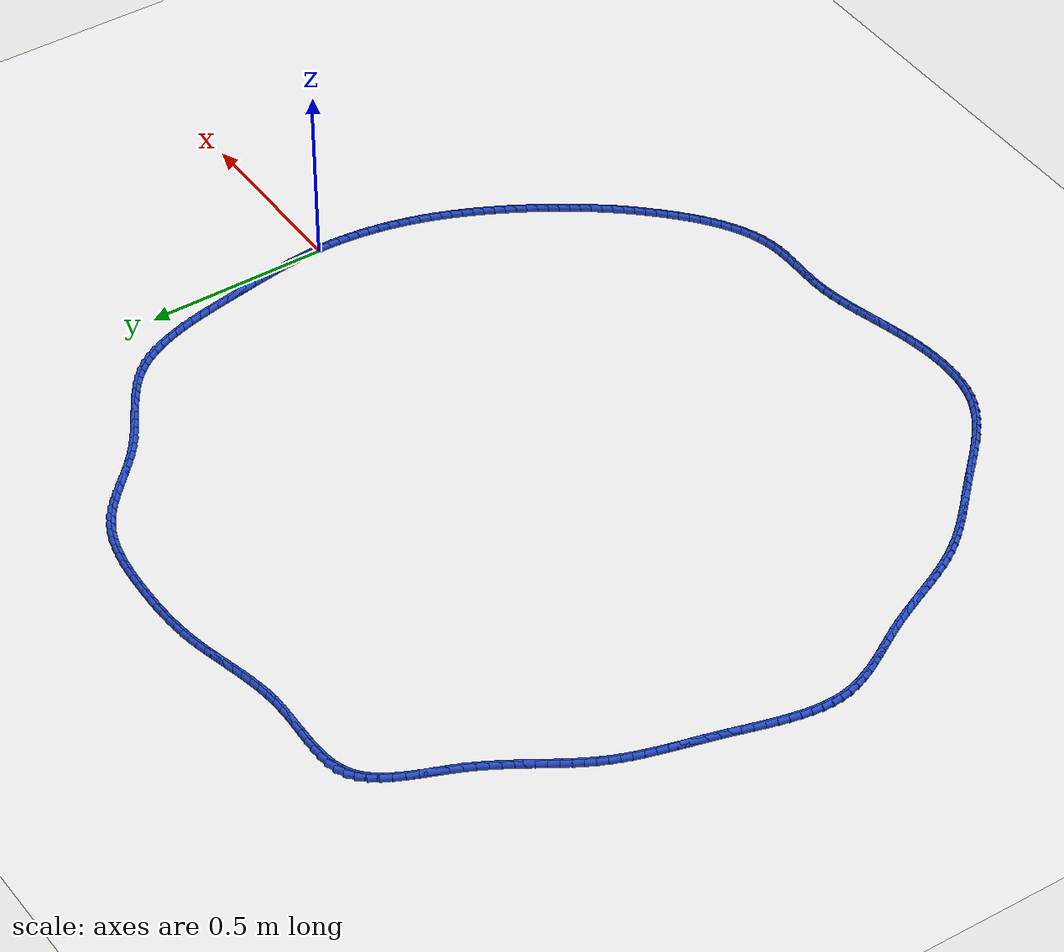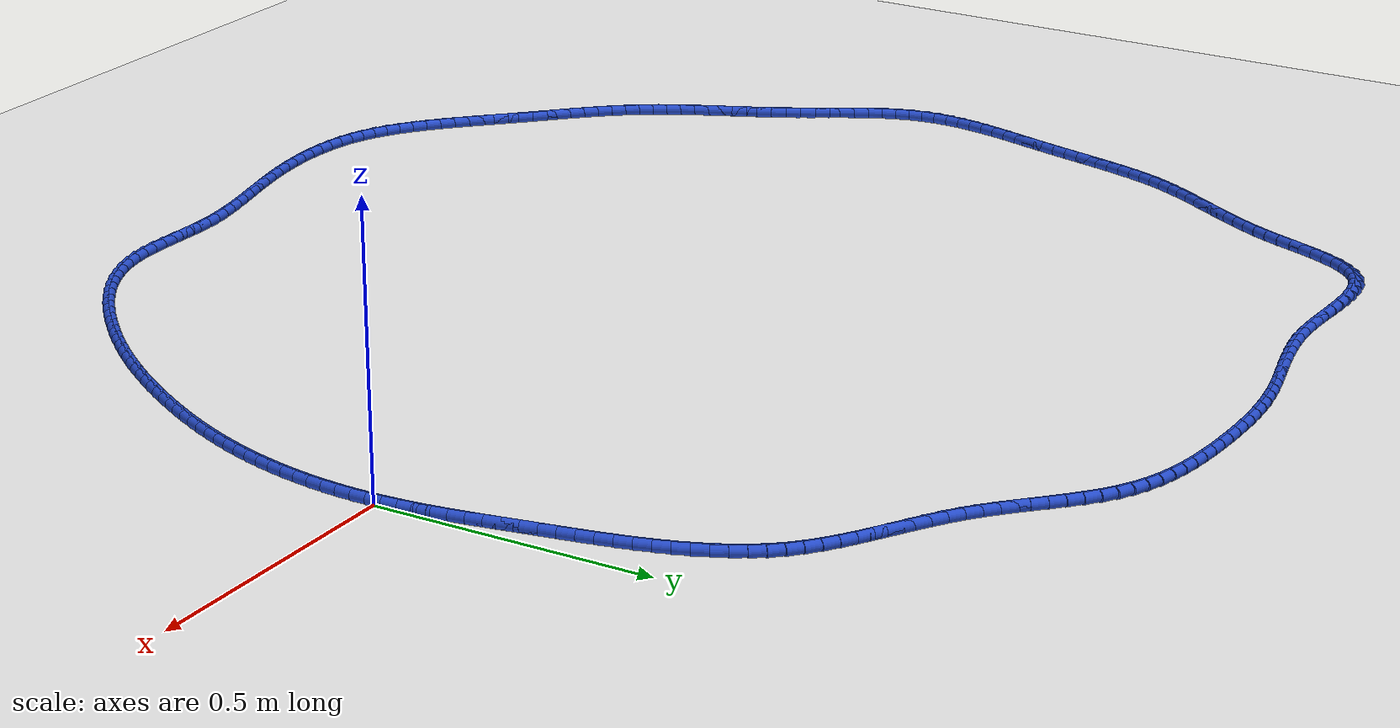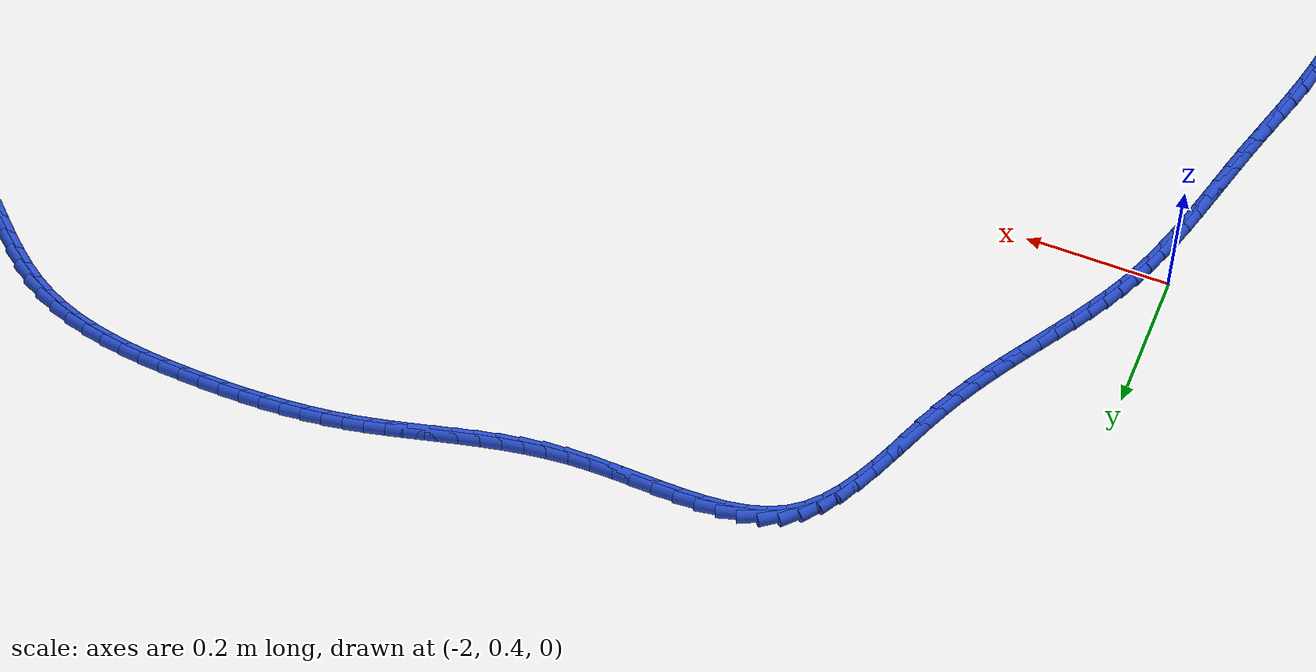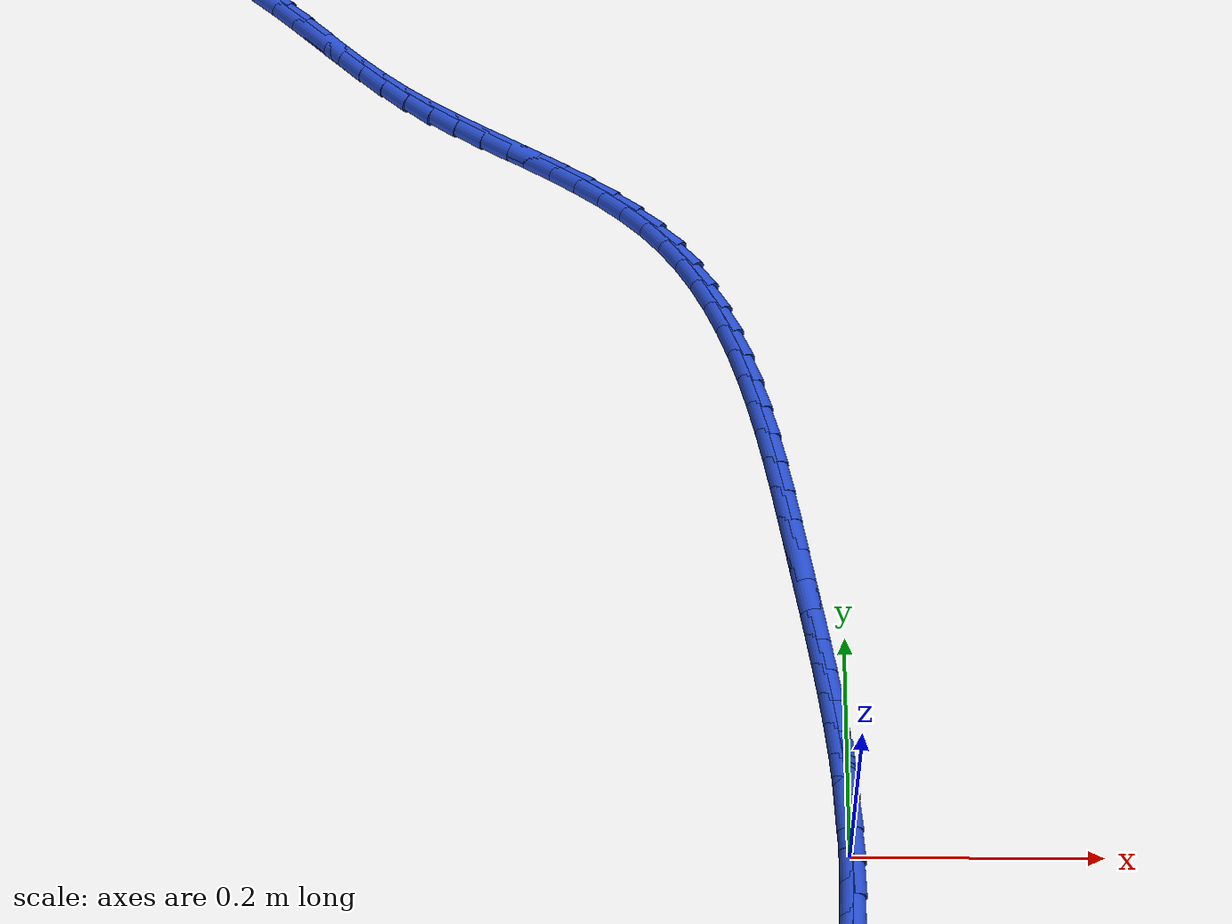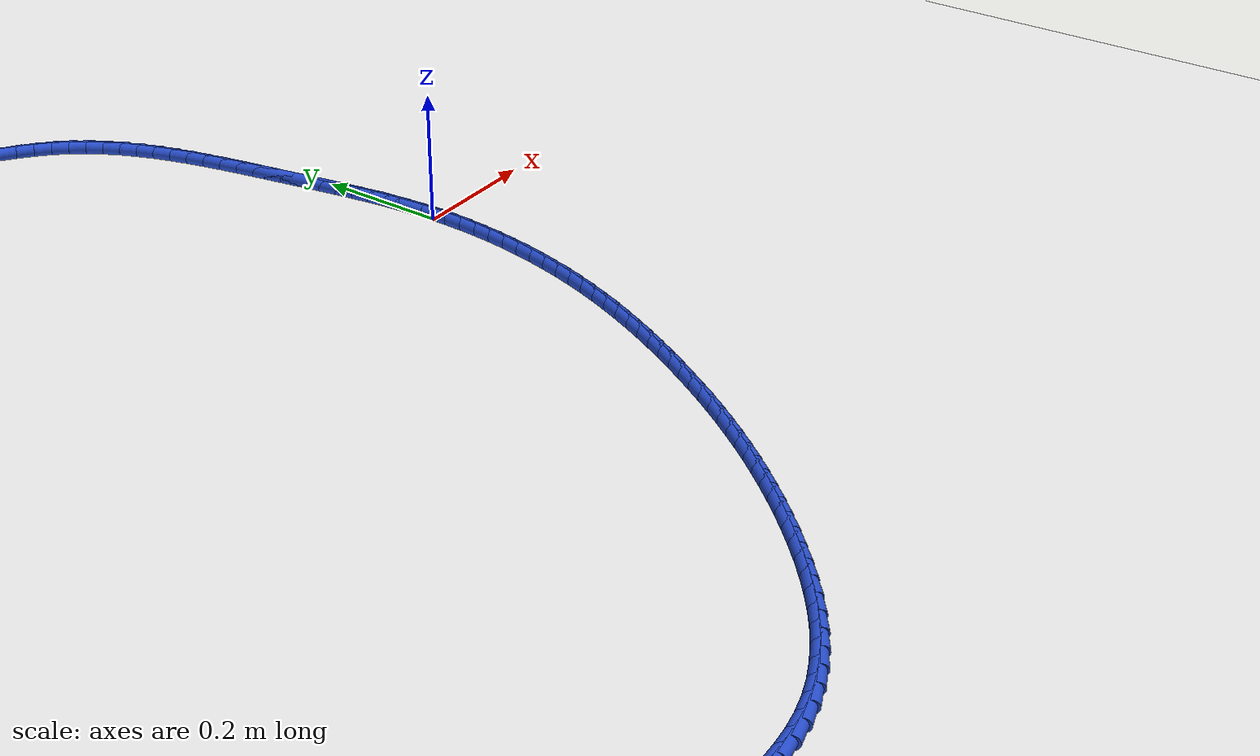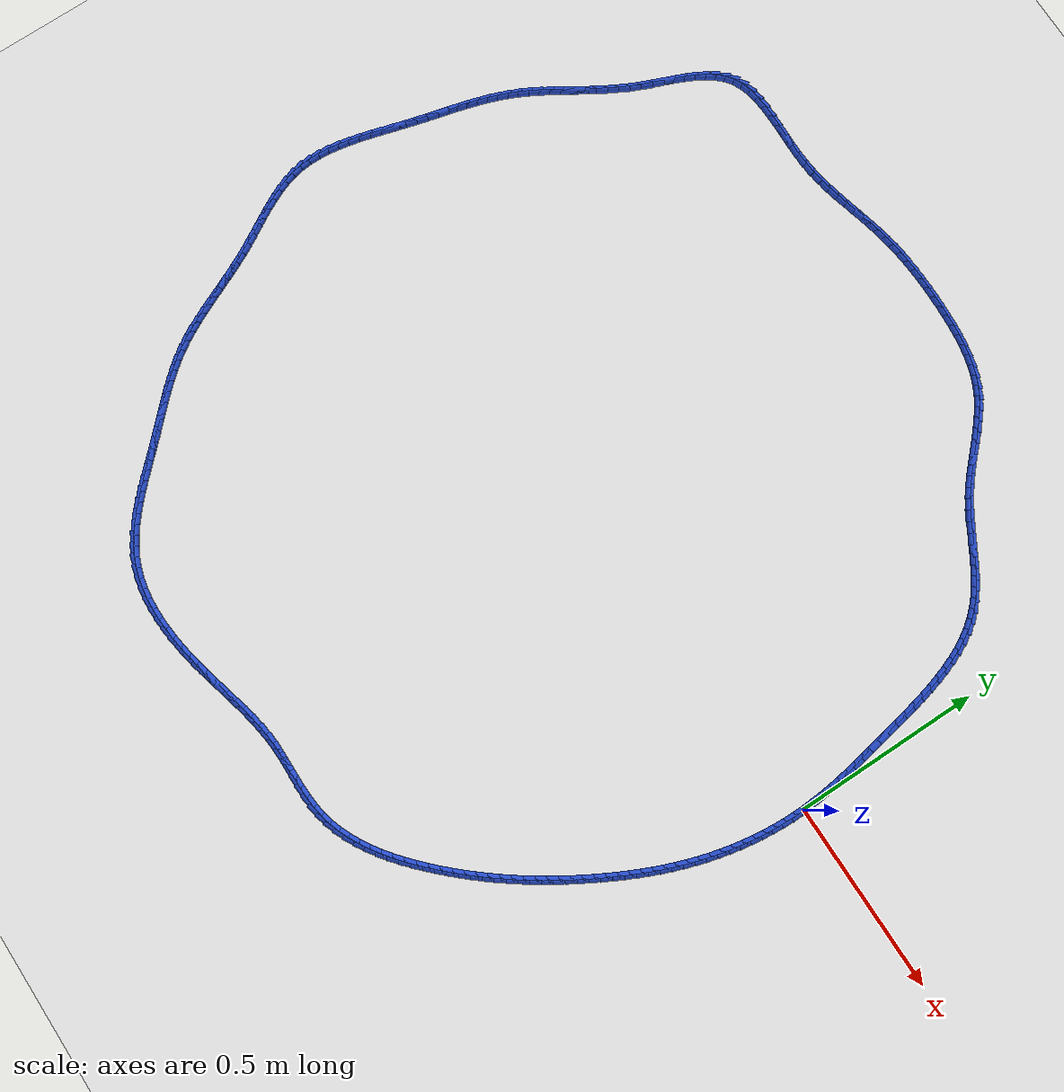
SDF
<sdf version="1.6">
 <world name="default">
  <light name="sun" type="directional">
   <pose>0 0 10 0 -0 0</pose>
   <diffuse>0.8 0.8 0.8 1</diffuse>
   <specular>0.2 0.2 0.2 1</specular>
   <attenuation>
    <range>1000</range>
    <constant>0.9</constant>
    <linear>0.01</linear>
    <quadratic>0.001</quadratic>
   </attenuation>
   <direction>-0.5 0.1 -0.9</direction>
  </light>
  <model name="ground_plane">
   <static>1</static>
   <link name="link">
    <collision name="collision">
     <geometry><plane><normal>0 0 1</normal><size>100 100</size></plane></geometry>
     <surface><friction><ode><mu>100</mu><mu2>50</mu2></ode></friction></surface>
    </collision>
    <visual name="visual">
     <cast_shadows>0</cast_shadows>
     <geometry><plane><normal>0 0 1</normal><size>100 100</size></plane></geometry>
     <material>
      <script><uri>file://media/materials/scripts/gazebo.material</uri><name>Gazebo/WhiteGlow</name></script>
     </material>
    </visual>
   </link>
  </model>
  <gravity>0 0 -9.8</gravity>
  <magnetic_field>6e-06 2.3e-05 -4.2e-05</magnetic_field>
  <atmosphere type="adiabatic"/>
  <physics name="default_physics" default="0" type="ode">
   <max_step_size>0.001</max_step_size>
   <real_time_factor>1</real_time_factor>
   <real_time_update_rate>1000</real_time_update_rate>
  </physics>
  <scene><ambient>0.4 0.4 0.4 1</ambient><background>0.7 0.7 0.7 1</background><shadows>1</shadows></scene>
  <spherical_coordinates>
   <surface_model>EARTH_WGS84</surface_model>
   <latitude_deg>0</latitude_deg>
   <longitude_deg>0</longitude_deg>
   <elevation>0</elevation>
   <heading_deg>0</heading_deg>
  </spherical_coordinates>
  <model name="line">
   <link name="link_0">
    <pose>-9.540979117872439e-18 -3.469446951953614e-17 0.01 0 1.57 -1.5294506513139627</pose>
    <collision name="collision">
     <geometry><cylinder><radius>0.01</radius><length>0.08</length></cylinder></geometry>
    </collision>
    <visual name="visual">
     <material>
      <script><name>Gazebo/Blue</name><uri>file://media/materials/scripts/gazebo.material</uri></script>
     </material>
     <geometry><cylinder><radius>0.01</radius><length>0.08</length></cylinder></geometry>
    </visual>
   </link>
   <link name="link_1">
    <pose>-0.0011748895653462578 0.02840006839639357 0.01 0 1.57 -1.496737372242825</pose>
    <collision name="collision">
     <geometry><cylinder><radius>0.01</radius><length>0.08</length></cylinder></geometry>
    </collision>
    <visual name="visual">
     <material>
      <script><name>Gazebo/Blue</name><uri>file://media/materials/scripts/gazebo.material</uri></script>
     </material>
     <geometry><cylinder><radius>0.01</radius><length>0.08</length></cylinder></geometry>
    </visual>
   </link>
   <link name="link_2">
    <pose>-0.0032738883289255174 0.05669050123774084 0.01 0 1.57 -1.468017511361112</pose>
    <collision name="collision">
     <geometry><cylinder><radius>0.01</radius><length>0.08</length></cylinder></geometry>
    </collision>
    <visual name="visual">
     <material>
      <script><name>Gazebo/Blue</name><uri>file://media/materials/scripts/gazebo.material</uri></script>
     </material>
     <geometry><cylinder><radius>0.01</radius><length>0.08</length></cylinder></geometry>
    </visual>
   </link>
   <link name="link_3">
    <pose>-0.006186115220526333 0.08492555365573844 0.01 0 1.57 -1.4434665865896867</pose>
    <collision name="collision">
     <geometry><cylinder><radius>0.01</radius><length>0.08</length></cylinder></geometry>
    </collision>
    <visual name="visual">
     <material>
      <script><name>Gazebo/Blue</name><uri>file://media/materials/scripts/gazebo.material</uri></script>
     </material>
     <geometry><cylinder><radius>0.01</radius><length>0.08</length></cylinder></geometry>
    </visual>
   </link>
   <link name="link_4">
    <pose>-0.009800689169937243 0.11315948078208297 0.01 0 1.57 -1.4231865035075302</pose>
    <collision name="collision">
     <geometry><cylinder><radius>0.01</radius><length>0.08</length></cylinder></geometry>
    </collision>
    <visual name="visual">
     <material>
      <script><name>Gazebo/Blue</name><uri>file://media/materials/scripts/gazebo.material</uri></script>
     </material>
     <geometry><cylinder><radius>0.01</radius><length>0.08</length></cylinder></geometry>
    </visual>
   </link>
   <link name="link_5">
    <pose>-0.01400672910694679 0.14144653774847116 0.01 0 1.57 -1.4072168435810375</pose>
    <collision name="collision">
     <geometry><cylinder><radius>0.01</radius><length>0.08</length></cylinder></geometry>
    </collision>
    <visual name="visual">
     <material>
      <script><name>Gazebo/Blue</name><uri>file://media/materials/scripts/gazebo.material</uri></script>
     </material>
     <geometry><cylinder><radius>0.01</radius><length>0.08</length></cylinder></geometry>
    </visual>
   </link>
   <link name="link_6">
    <pose>-0.018693353961343515 0.16984097968659945 0.01 0 1.57 -1.3955461636745663</pose>
    <collision name="collision">
     <geometry><cylinder><radius>0.01</radius><length>0.08</length></cylinder></geometry>
    </collision>
    <visual name="visual">
     <material>
      <script><name>Gazebo/Blue</name><uri>file://media/materials/scripts/gazebo.material</uri></script>
     </material>
     <geometry><cylinder><radius>0.01</radius><length>0.08</length></cylinder></geometry>
    </visual>
   </link>
   <link name="link_7">
    <pose>-0.02374968266291596 0.19839706172816468 0.01 0 1.57 -1.3881221389597653</pose>
    <collision name="collision">
     <geometry><cylinder><radius>0.01</radius><length>0.08</length></cylinder></geometry>
    </collision>
    <visual name="visual">
     <material>
      <script><name>Gazebo/Blue</name><uri>file://media/materials/scripts/gazebo.material</uri></script>
     </material>
     <geometry><cylinder><radius>0.01</radius><length>0.08</length></cylinder></geometry>
    </visual>
   </link>
   <link name="link_8">
    <pose>-0.02906483414145267 0.22716903900486332 0.01 0 1.57 -1.3848598721502252</pose>
    <collision name="collision">
     <geometry><cylinder><radius>0.01</radius><length>0.08</length></cylinder></geometry>
    </collision>
    <visual name="visual">
     <material>
      <script><name>Gazebo/Blue</name><uri>file://media/materials/scripts/gazebo.material</uri></script>
     </material>
     <geometry><cylinder><radius>0.01</radius><length>0.08</length></cylinder></geometry>
    </visual>
   </link>
   <link name="link_9">
    <pose>-0.034527927326742196 0.25621116664839216 0.01 0 1.57 -1.385393767877527</pose>
    <collision name="collision">
     <geometry><cylinder><radius>0.01</radius><length>0.08</length></cylinder></geometry>
    </collision>
    <visual name="visual">
     <material>
      <script><name>Gazebo/Blue</name><uri>file://media/materials/scripts/gazebo.material</uri></script>
     </material>
     <geometry><cylinder><radius>0.01</radius><length>0.08</length></cylinder></geometry>
    </visual>
   </link>
   <link name="link_10">
    <pose>-0.04003479357177395 0.28557226788144513 0.01 0 1.57 -1.3846859534579163</pose>
    <collision name="collision">
     <geometry><cylinder><radius>0.01</radius><length>0.08</length></cylinder></geometry>
    </collision>
    <visual name="visual">
     <material>
      <script><name>Gazebo/Blue</name><uri>file://media/materials/scripts/gazebo.material</uri></script>
     </material>
     <geometry><cylinder><radius>0.01</radius><length>0.08</length></cylinder></geometry>
    </visual>
   </link>
   <link name="link_11">
    <pose>-0.0456124408212615 0.3151950136046437 0.01 0 1.57 -1.3782954925352733</pose>
    <collision name="collision">
     <geometry><cylinder><radius>0.01</radius><length>0.08</length></cylinder></geometry>
    </collision>
    <visual name="visual">
     <material>
      <script><name>Gazebo/Blue</name><uri>file://media/materials/scripts/gazebo.material</uri></script>
     </material>
     <geometry><cylinder><radius>0.01</radius><length>0.08</length></cylinder></geometry>
    </visual>
   </link>
   <link name="link_12">
    <pose>-0.05140732464027866 0.34492541385785136 0.01 0 1.57 -1.3660632757519449</pose>
    <collision name="collision">
     <geometry><cylinder><radius>0.01</radius><length>0.08</length></cylinder></geometry>
    </collision>
    <visual name="visual">
     <material>
      <script><name>Gazebo/Blue</name><uri>file://media/materials/scripts/gazebo.material</uri></script>
     </material>
     <geometry><cylinder><radius>0.01</radius><length>0.08</length></cylinder></geometry>
    </visual>
   </link>
   <link name="link_13">
    <pose>-0.05757026076933132 0.3746059502865687 0.01 0 1.57 -1.3478566417226272</pose>
    <collision name="collision">
     <geometry><cylinder><radius>0.01</radius><length>0.08</length></cylinder></geometry>
    </collision>
    <visual name="visual">
     <material>
      <script><name>Gazebo/Blue</name><uri>file://media/materials/scripts/gazebo.material</uri></script>
     </material>
     <geometry><cylinder><radius>0.01</radius><length>0.08</length></cylinder></geometry>
    </visual>
   </link>
   <link name="link_14">
    <pose>-0.06425206494892545 0.40407910453629703 0.01 0 1.57 -1.3234126970885531</pose>
    <collision name="collision">
     <geometry><cylinder><radius>0.01</radius><length>0.08</length></cylinder></geometry>
    </collision>
    <visual name="visual">
     <material>
      <script><name>Gazebo/Blue</name><uri>file://media/materials/scripts/gazebo.material</uri></script>
     </material>
     <geometry><cylinder><radius>0.01</radius><length>0.08</length></cylinder></geometry>
    </visual>
   </link>
   <link name="link_15">
    <pose>-0.07160355291956694 0.43318735825253707 0.01 0 1.57 -1.2923477020681833</pose>
    <collision name="collision">
     <geometry><cylinder><radius>0.01</radius><length>0.08</length></cylinder></geometry>
    </collision>
    <visual name="visual">
     <material>
      <script><name>Gazebo/Blue</name><uri>file://media/materials/scripts/gazebo.material</uri></script>
     </material>
     <geometry><cylinder><radius>0.01</radius><length>0.08</length></cylinder></geometry>
    </visual>
   </link>
   <link name="link_16">
    <pose>-0.0797755404217617 0.46177319308078957 0.01 0 1.57 -1.2541715530515547</pose>
    <collision name="collision">
     <geometry><cylinder><radius>0.01</radius><length>0.08</length></cylinder></geometry>
    </collision>
    <visual name="visual">
     <material>
      <script><name>Gazebo/Blue</name><uri>file://media/materials/scripts/gazebo.material</uri></script>
     </material>
     <geometry><cylinder><radius>0.01</radius><length>0.08</length></cylinder></geometry>
    </visual>
   </link>
   <link name="link_17">
    <pose>-0.08891884319601567 0.48967909066655546 0.01 0 1.57 -1.2083136573844964</pose>
    <collision name="collision">
     <geometry><cylinder><radius>0.01</radius><length>0.08</length></cylinder></geometry>
    </collision>
    <visual name="visual">
     <material>
      <script><name>Gazebo/Blue</name><uri>file://media/materials/scripts/gazebo.material</uri></script>
     </material>
     <geometry><cylinder><radius>0.01</radius><length>0.08</length></cylinder></geometry>
    </visual>
   </link>
   <link name="link_18">
    <pose>-0.09918427698283475 0.5167475326553356 0.01 0 1.57 -1.1541689465700455</pose>
    <collision name="collision">
     <geometry><cylinder><radius>0.01</radius><length>0.08</length></cylinder></geometry>
    </collision>
    <visual name="visual">
     <material>
      <script><name>Gazebo/Blue</name><uri>file://media/materials/scripts/gazebo.material</uri></script>
     </material>
     <geometry><cylinder><radius>0.01</radius><length>0.08</length></cylinder></geometry>
    </visual>
   </link>
   <link name="link_19">
    <pose>-0.11072265752272481 0.5428210006926305 0.01 0 1.57 -1.0911748389295841</pose>
    <collision name="collision">
     <geometry><cylinder><radius>0.01</radius><length>0.08</length></cylinder></geometry>
    </collision>
    <visual name="visual">
     <material>
      <script><name>Gazebo/Blue</name><uri>file://media/materials/scripts/gazebo.material</uri></script>
     </material>
     <geometry><cylinder><radius>0.01</radius><length>0.08</length></cylinder></geometry>
    </visual>
   </link>
   <link name="link_20">
    <pose>-0.12368480055619191 0.5677419764239418 0.01 0 1.57 -1.0189295101047202</pose>
    <collision name="collision">
     <geometry><cylinder><radius>0.01</radius><length>0.08</length></cylinder></geometry>
    </collision>
    <visual name="visual">
     <material>
      <script><name>Gazebo/Blue</name><uri>file://media/materials/scripts/gazebo.material</uri></script>
     </material>
     <geometry><cylinder><radius>0.01</radius><length>0.08</length></cylinder></geometry>
    </visual>
   </link>
   <link name="link_21">
    <pose>-0.13822152182374187 0.5913529414947698 0.01 0 1.57 -0.9373549128229389</pose>
    <collision name="collision">
     <geometry><cylinder><radius>0.01</radius><length>0.08</length></cylinder></geometry>
    </collision>
    <visual name="visual">
     <material>
      <script><name>Gazebo/Blue</name><uri>file://media/materials/scripts/gazebo.material</uri></script>
     </material>
     <geometry><cylinder><radius>0.01</radius><length>0.08</length></cylinder></geometry>
    </visual>
   </link>
   <link name="link_22">
    <pose>-0.15448363706588064 0.6134963775506154 0.01 0 1.57 -0.8469456136217031</pose>
    <collision name="collision">
     <geometry><cylinder><radius>0.01</radius><length>0.08</length></cylinder></geometry>
    </collision>
    <visual name="visual">
     <material>
      <script><name>Gazebo/Blue</name><uri>file://media/materials/scripts/gazebo.material</uri></script>
     </material>
     <geometry><cylinder><radius>0.01</radius><length>0.08</length></cylinder></geometry>
    </visual>
   </link>
   <link name="link_23">
    <pose>-0.172620886011357 0.6340158584470451 0.01 0 1.57 -0.7559809131656215</pose>
    <collision name="collision">
     <geometry><cylinder><radius>0.01</radius><length>0.08</length></cylinder></geometry>
    </collision>
    <visual name="visual">
     <material>
      <script><name>Gazebo/Blue</name><uri>file://media/materials/scripts/gazebo.material</uri></script>
     </material>
     <geometry><cylinder><radius>0.01</radius><length>0.08</length></cylinder></geometry>
    </visual>
   </link>
   <link name="link_24">
    <pose>-0.19264491560713903 0.6528951296736946 0.01 0 1.57 -0.6797770874953046</pose>
    <collision name="collision">
     <geometry><cylinder><radius>0.01</radius><length>0.08</length></cylinder></geometry>
    </collision>
    <visual name="visual">
     <material>
      <script><name>Gazebo/Blue</name><uri>file://media/materials/scripts/gazebo.material</uri></script>
     </material>
     <geometry><cylinder><radius>0.01</radius><length>0.08</length></cylinder></geometry>
    </visual>
   </link>
   <link name="link_25">
    <pose>-0.21429482104517897 0.6703945914763423 0.01 0 1.57 -0.6201363817404948</pose>
    <collision name="collision">
     <geometry><cylinder><radius>0.01</radius><length>0.08</length></cylinder></geometry>
    </collision>
    <visual name="visual">
     <material>
      <script><name>Gazebo/Blue</name><uri>file://media/materials/scripts/gazebo.material</uri></script>
     </material>
     <geometry><cylinder><radius>0.01</radius><length>0.08</length></cylinder></geometry>
    </visual>
   </link>
   <link name="link_26">
    <pose>-0.23727776657671398 0.6868070557306853 0.01 0 1.57 -0.5764697680447343</pose>
    <collision name="collision">
     <geometry><cylinder><radius>0.01</radius><length>0.08</length></cylinder></geometry>
    </collision>
    <visual name="visual">
     <material>
      <script><name>Gazebo/Blue</name><uri>file://media/materials/scripts/gazebo.material</uri></script>
     </material>
     <geometry><cylinder><radius>0.01</radius><length>0.08</length></cylinder></geometry>
    </visual>
   </link>
   <link name="link_27">
    <pose>-0.26130091645298115 0.7024253343124204 0.01 0 1.57 -0.5479426658410158</pose>
    <collision name="collision">
     <geometry><cylinder><radius>0.01</radius><length>0.08</length></cylinder></geometry>
    </collision>
    <visual name="visual">
     <material>
      <script><name>Gazebo/Blue</name><uri>file://media/materials/scripts/gazebo.material</uri></script>
     </material>
     <geometry><cylinder><radius>0.01</radius><length>0.08</length></cylinder></geometry>
    </visual>
   </link>
   <link name="link_28">
    <pose>-0.2860714349252176 0.7175422390972441 0.01 0 1.57 -0.5337854872727317</pose>
    <collision name="collision">
     <geometry><cylinder><radius>0.01</radius><length>0.08</length></cylinder></geometry>
    </collision>
    <visual name="visual">
     <material>
      <script><name>Gazebo/Blue</name><uri>file://media/materials/scripts/gazebo.material</uri></script>
     </material>
     <geometry><cylinder><radius>0.01</radius><length>0.08</length></cylinder></geometry>
    </visual>
   </link>
   <link name="link_29">
    <pose>-0.31129648624466033 0.7324505819608536 0.01 0 1.57 -0.533455093219091</pose>
    <collision name="collision">
     <geometry><cylinder><radius>0.01</radius><length>0.08</length></cylinder></geometry>
    </collision>
    <visual name="visual">
     <material>
      <script><name>Gazebo/Blue</name><uri>file://media/materials/scripts/gazebo.material</uri></script>
     </material>
     <geometry><cylinder><radius>0.01</radius><length>0.08</length></cylinder></geometry>
    </visual>
   </link>
   <link name="link_30">
    <pose>-0.3366832346625466 0.7474431747789455 0.01 0 1.57 -0.5466927672343924</pose>
    <collision name="collision">
     <geometry><cylinder><radius>0.01</radius><length>0.08</length></cylinder></geometry>
    </collision>
    <visual name="visual">
     <material>
      <script><name>Gazebo/Blue</name><uri>file://media/materials/scripts/gazebo.material</uri></script>
     </material>
     <geometry><cylinder><radius>0.01</radius><length>0.08</length></cylinder></geometry>
    </visual>
   </link>
   <link name="link_31">
    <pose>-0.36193884443011365 0.7628128294272165 0.01 0 1.57 -0.5735095934364645</pose>
    <collision name="collision">
     <geometry><cylinder><radius>0.01</radius><length>0.08</length></cylinder></geometry>
    </collision>
    <visual name="visual">
     <material>
      <script><name>Gazebo/Blue</name><uri>file://media/materials/scripts/gazebo.material</uri></script>
     </material>
     <geometry><cylinder><radius>0.01</radius><length>0.08</length></cylinder></geometry>
    </visual>
   </link>
   <link name="link_32">
    <pose>-0.38677047979859847 0.7788523577813637 0.01 0 1.57 -0.6141087539292146</pose>
    <collision name="collision">
     <geometry><cylinder><radius>0.01</radius><length>0.08</length></cylinder></geometry>
    </collision>
    <visual name="visual">
     <material>
      <script><name>Gazebo/Blue</name><uri>file://media/materials/scripts/gazebo.material</uri></script>
     </material>
     <geometry><cylinder><radius>0.01</radius><length>0.08</length></cylinder></geometry>
    </visual>
   </link>
   <link name="link_33">
    <pose>-0.41088530501923803 0.7958545717170833 0.01 0 1.57 -0.6671068904608767</pose>
    <collision name="collision">
     <geometry><cylinder><radius>0.01</radius><length>0.08</length></cylinder></geometry>
    </collision>
    <visual name="visual">
     <material>
      <script><name>Gazebo/Blue</name><uri>file://media/materials/scripts/gazebo.material</uri></script>
     </material>
     <geometry><cylinder><radius>0.01</radius><length>0.08</length></cylinder></geometry>
    </visual>
   </link>
   <link name="link_34">
    <pose>-0.4340206537252782 0.8140749523762698 0.01 0 1.57 -0.7149941939985172</pose>
    <collision name="collision">
     <geometry><cylinder><radius>0.01</radius><length>0.08</length></cylinder></geometry>
    </collision>
    <visual name="visual">
     <material>
      <script><name>Gazebo/Blue</name><uri>file://media/materials/scripts/gazebo.material</uri></script>
     </material>
     <geometry><cylinder><radius>0.01</radius><length>0.08</length></cylinder></geometry>
    </visual>
   </link>
   <link name="link_35">
    <pose>-0.45623929883126485 0.8333662916055669 0.01 0 1.57 -0.74704112518149</pose>
    <collision name="collision">
     <geometry><cylinder><radius>0.01</radius><length>0.08</length></cylinder></geometry>
    </collision>
    <visual name="visual">
     <material>
      <script><name>Gazebo/Blue</name><uri>file://media/materials/scripts/gazebo.material</uri></script>
     </material>
     <geometry><cylinder><radius>0.01</radius><length>0.08</length></cylinder></geometry>
    </visual>
   </link>
   <link name="link_36">
    <pose>-0.47780256200934385 0.8533357026754125 0.01 0 1.57 -0.7631692323247999</pose>
    <collision name="collision">
     <geometry><cylinder><radius>0.01</radius><length>0.08</length></cylinder></geometry>
    </collision>
    <visual name="visual">
     <material>
      <script><name>Gazebo/Blue</name><uri>file://media/materials/scripts/gazebo.material</uri></script>
     </material>
     <geometry><cylinder><radius>0.01</radius><length>0.08</length></cylinder></geometry>
    </visual>
   </link>
   <link name="link_37">
    <pose>-0.49897459717535686 0.8735867943185851 0.01 0 1.57 -0.7633388351855224</pose>
    <collision name="collision">
     <geometry><cylinder><radius>0.01</radius><length>0.08</length></cylinder></geometry>
    </collision>
    <visual name="visual">
     <material>
      <script><name>Gazebo/Blue</name><uri>file://media/materials/scripts/gazebo.material</uri></script>
     </material>
     <geometry><cylinder><radius>0.01</radius><length>0.08</length></cylinder></geometry>
    </visual>
   </link>
   <link name="link_38">
    <pose>-0.5200195582451452 0.8937231752678623 0.01 0 1.57 -0.7472675693725204</pose>
    <collision name="collision">
     <geometry><cylinder><radius>0.01</radius><length>0.08</length></cylinder></geometry>
    </collision>
    <visual name="visual">
     <material>
      <script><name>Gazebo/Blue</name><uri>file://media/materials/scripts/gazebo.material</uri></script>
     </material>
     <geometry><cylinder><radius>0.01</radius><length>0.08</length></cylinder></geometry>
    </visual>
   </link>
   <link name="link_39">
    <pose>-0.5412015991345507 0.9133484542560212 0.01 0 1.57 -0.7144155490018477</pose>
    <collision name="collision">
     <geometry><cylinder><radius>0.01</radius><length>0.08</length></cylinder></geometry>
    </collision>
    <visual name="visual">
     <material>
      <script><name>Gazebo/Blue</name><uri>file://media/materials/scripts/gazebo.material</uri></script>
     </material>
     <geometry><cylinder><radius>0.01</radius><length>0.08</length></cylinder></geometry>
    </visual>
   </link>
   <link name="link_40">
    <pose>-0.5627848737594149 0.9320662400158399 0.01 0 1.57 -0.6640992526576575</pose>
    <collision name="collision">
     <geometry><cylinder><radius>0.01</radius><length>0.08</length></cylinder></geometry>
    </collision>
    <visual name="visual">
     <material>
      <script><name>Gazebo/Blue</name><uri>file://media/materials/scripts/gazebo.material</uri></script>
     </material>
     <geometry><cylinder><radius>0.01</radius><length>0.08</length></cylinder></geometry>
    </visual>
   </link>
   <link name="link_41">
    <pose>-0.5850335360355793 0.9494801412800963 0.01 0 1.57 -0.5957723991119743</pose>
    <collision name="collision">
     <geometry><cylinder><radius>0.01</radius><length>0.08</length></cylinder></geometry>
    </collision>
    <visual name="visual">
     <material>
      <script><name>Gazebo/Blue</name><uri>file://media/materials/scripts/gazebo.material</uri></script>
     </material>
     <geometry><cylinder><radius>0.01</radius><length>0.08</length></cylinder></geometry>
    </visual>
   </link>
   <link name="link_42">
    <pose>-0.6082117398788853 0.9651937667815672 0.01 0 1.57 -0.5097018519666382</pose>
    <collision name="collision">
     <geometry><cylinder><radius>0.01</radius><length>0.08</length></cylinder></geometry>
    </collision>
    <visual name="visual">
     <material>
      <script><name>Gazebo/Blue</name><uri>file://media/materials/scripts/gazebo.material</uri></script>
     </material>
     <geometry><cylinder><radius>0.01</radius><length>0.08</length></cylinder></geometry>
    </visual>
   </link>
   <link name="link_43">
    <pose>-0.6325804593131206 0.9788150852497046 0.01 0 1.57 -0.41726505626515326</pose>
    <collision name="collision">
     <geometry><cylinder><radius>0.01</radius><length>0.08</length></cylinder></geometry>
    </collision>
    <visual name="visual">
     <material>
      <script><name>Gazebo/Blue</name><uri>file://media/materials/scripts/gazebo.material</uri></script>
     </material>
     <geometry><cylinder><radius>0.01</radius><length>0.08</length></cylinder></geometry>
    </visual>
   </link>
   <link name="link_44">
    <pose>-0.6582303542764387 0.9901855855568369 0.01 0 1.57 -0.3346343525376232</pose>
    <collision name="collision">
     <geometry><cylinder><radius>0.01</radius><length>0.08</length></cylinder></geometry>
    </collision>
    <visual name="visual">
     <material>
      <script><name>Gazebo/Blue</name><uri>file://media/materials/scripts/gazebo.material</uri></script>
     </material>
     <geometry><cylinder><radius>0.01</radius><length>0.08</length></cylinder></geometry>
    </visual>
   </link>
   <link name="link_45">
    <pose>-0.6849992449645556 0.9994934288576187 0.01 0 1.57 -0.26307403307249666</pose>
    <collision name="collision">
     <geometry><cylinder><radius>0.01</radius><length>0.08</length></cylinder></geometry>
    </collision>
    <visual name="visual">
     <material>
      <script><name>Gazebo/Blue</name><uri>file://media/materials/scripts/gazebo.material</uri></script>
     </material>
     <geometry><cylinder><radius>0.01</radius><length>0.08</length></cylinder></geometry>
    </visual>
   </link>
   <link name="link_46">
    <pose>-0.7127044545278166 1.006954880106492 0.01 0 1.57 -0.20210618442431727</pose>
    <collision name="collision">
     <geometry><cylinder><radius>0.01</radius><length>0.08</length></cylinder></geometry>
    </collision>
    <visual name="visual">
     <material>
      <script><name>Gazebo/Blue</name><uri>file://media/materials/scripts/gazebo.material</uri></script>
     </material>
     <geometry><cylinder><radius>0.01</radius><length>0.08</length></cylinder></geometry>
    </visual>
   </link>
   <link name="link_47">
    <pose>-0.741163306116567 1.0127862042579001 0.01 0 1.57 -0.15101134307420294</pose>
    <collision name="collision">
     <geometry><cylinder><radius>0.01</radius><length>0.08</length></cylinder></geometry>
    </collision>
    <visual name="visual">
     <material>
      <script><name>Gazebo/Blue</name><uri>file://media/materials/scripts/gazebo.material</uri></script>
     </material>
     <geometry><cylinder><radius>0.01</radius><length>0.08</length></cylinder></geometry>
    </visual>
   </link>
   <link name="link_48">
    <pose>-0.7701931228811515 1.017203666266285 0.01 0 1.57 -0.10901785737317916</pose>
    <collision name="collision">
     <geometry><cylinder><radius>0.01</radius><length>0.08</length></cylinder></geometry>
    </collision>
    <visual name="visual">
     <material>
      <script><name>Gazebo/Blue</name><uri>file://media/materials/scripts/gazebo.material</uri></script>
     </material>
     <geometry><cylinder><radius>0.01</radius><length>0.08</length></cylinder></geometry>
    </visual>
   </link>
   <link name="link_49">
    <pose>-0.7996112279719153 1.0204235310860883 0.01 0 1.57 -0.075422215549036</pose>
    <collision name="collision">
     <geometry><cylinder><radius>0.01</radius><length>0.08</length></cylinder></geometry>
    </collision>
    <visual name="visual">
     <material>
      <script><name>Gazebo/Blue</name><uri>file://media/materials/scripts/gazebo.material</uri></script>
     </material>
     <geometry><cylinder><radius>0.01</radius><length>0.08</length></cylinder></geometry>
    </visual>
   </link>
   <link name="link_50">
    <pose>-0.8292349445392038 1.0226620636717534 0.01 0 1.57 -0.049660039171751005</pose>
    <collision name="collision">
     <geometry><cylinder><radius>0.01</radius><length>0.08</length></cylinder></geometry>
    </collision>
    <visual name="visual">
     <material>
      <script><name>Gazebo/Blue</name><uri>file://media/materials/scripts/gazebo.material</uri></script>
     </material>
     <geometry><cylinder><radius>0.01</radius><length>0.08</length></cylinder></geometry>
    </visual>
   </link>
   <link name="link_51">
    <pose>-0.8588815957333616 1.0241355289777219 0.01 0 1.57 -0.03040756893025305</pose>
    <collision name="collision">
     <geometry><cylinder><radius>0.01</radius><length>0.08</length></cylinder></geometry>
    </collision>
    <visual name="visual">
     <material>
      <script><name>Gazebo/Blue</name><uri>file://media/materials/scripts/gazebo.material</uri></script>
     </material>
     <geometry><cylinder><radius>0.01</radius><length>0.08</length></cylinder></geometry>
    </visual>
   </link>
   <link name="link_52">
    <pose>-0.888384982638496 1.0250329318513889 0.01 0 1.57 -0.011195536878011326</pose>
    <collision name="collision">
     <geometry><cylinder><radius>0.01</radius><length>0.08</length></cylinder></geometry>
    </collision>
    <visual name="visual">
     <material>
      <script><name>Gazebo/Blue</name><uri>file://media/materials/scripts/gazebo.material</uri></script>
     </material>
     <geometry><cylinder><radius>0.01</radius><length>0.08</length></cylinder></geometry>
    </visual>
   </link>
   <link name="link_53">
    <pose>-0.9176890750583393 1.0253610206064196 0.01 0 1.57 0.010627564616894666</pose>
    <collision name="collision">
     <geometry><cylinder><radius>0.01</radius><length>0.08</length></cylinder></geometry>
    </collision>
    <visual name="visual">
     <material>
      <script><name>Gazebo/Blue</name><uri>file://media/materials/scripts/gazebo.material</uri></script>
     </material>
     <geometry><cylinder><radius>0.01</radius><length>0.08</length></cylinder></geometry>
    </visual>
   </link>
   <link name="link_54">
    <pose>-0.9467830162954546 1.0250518112246432 0.01 0 1.57 0.03512964764408823</pose>
    <collision name="collision">
     <geometry><cylinder><radius>0.01</radius><length>0.08</length></cylinder></geometry>
    </collision>
    <visual name="visual">
     <material>
      <script><name>Gazebo/Blue</name><uri>file://media/materials/scripts/gazebo.material</uri></script>
     </material>
     <geometry><cylinder><radius>0.01</radius><length>0.08</length></cylinder></geometry>
    </visual>
   </link>
   <link name="link_55">
    <pose>-0.9756560866892376 1.0240370929823568 0.01 0 1.57 0.06236126289444396</pose>
    <collision name="collision">
     <geometry><cylinder><radius>0.01</radius><length>0.08</length></cylinder></geometry>
    </collision>
    <visual name="visual">
     <material>
      <script><name>Gazebo/Blue</name><uri>file://media/materials/scripts/gazebo.material</uri></script>
     </material>
     <geometry><cylinder><radius>0.01</radius><length>0.08</length></cylinder></geometry>
    </visual>
   </link>
   <link name="link_56">
    <pose>-1.0042975665790854 1.0222486551558572 0.01 0 1.57 0.09235780207010844</pose>
    <collision name="collision">
     <geometry><cylinder><radius>0.01</radius><length>0.08</length></cylinder></geometry>
    </collision>
    <visual name="visual">
     <material>
      <script><name>Gazebo/Blue</name><uri>file://media/materials/scripts/gazebo.material</uri></script>
     </material>
     <geometry><cylinder><radius>0.01</radius><length>0.08</length></cylinder></geometry>
    </visual>
   </link>
   <link name="link_57">
    <pose>-1.0326967363043935 1.0196182870214412 0.01 0 1.57 0.12513298274729653</pose>
    <collision name="collision">
     <geometry><cylinder><radius>0.01</radius><length>0.08</length></cylinder></geometry>
    </collision>
    <visual name="visual">
     <material>
      <script><name>Gazebo/Blue</name><uri>file://media/materials/scripts/gazebo.material</uri></script>
     </material>
     <geometry><cylinder><radius>0.01</radius><length>0.08</length></cylinder></geometry>
    </visual>
   </link>
   <link name="link_58">
    <pose>-1.0608428762045576 1.016077777855406 0.01 0 1.57 0.1606612151877009</pose>
    <collision name="collision">
     <geometry><cylinder><radius>0.01</radius><length>0.08</length></cylinder></geometry>
    </collision>
    <visual name="visual">
     <material>
      <script><name>Gazebo/Blue</name><uri>file://media/materials/scripts/gazebo.material</uri></script>
     </material>
     <geometry><cylinder><radius>0.01</radius><length>0.08</length></cylinder></geometry>
    </visual>
   </link>
   <link name="link_59">
    <pose>-1.0887253640423424 1.0115591985149877 0.01 0 1.57 0.1956345536778979</pose>
    <collision name="collision">
     <geometry><cylinder><radius>0.01</radius><length>0.08</length></cylinder></geometry>
    </collision>
    <visual name="visual">
     <material>
      <script><name>Gazebo/Blue</name><uri>file://media/materials/scripts/gazebo.material</uri></script>
     </material>
     <geometry><cylinder><radius>0.01</radius><length>0.08</length></cylinder></geometry>
    </visual>
   </link>
   <link name="link_60">
    <pose>-1.1163638455622071 1.0060821028397198 0.01 0 1.57 0.22202229952930339</pose>
    <collision name="collision">
     <geometry><cylinder><radius>0.01</radius><length>0.08</length></cylinder></geometry>
    </collision>
    <visual name="visual">
     <material>
      <script><name>Gazebo/Blue</name><uri>file://media/materials/scripts/gazebo.material</uri></script>
     </material>
     <geometry><cylinder><radius>0.01</radius><length>0.08</length></cylinder></geometry>
    </visual>
   </link>
   <link name="link_61">
    <pose>-1.14385097299019 0.999877053939564 0.01 0 1.57 0.238501276424082</pose>
    <collision name="collision">
     <geometry><cylinder><radius>0.01</radius><length>0.08</length></cylinder></geometry>
    </collision>
    <visual name="visual">
     <material>
      <script><name>Gazebo/Blue</name><uri>file://media/materials/scripts/gazebo.material</uri></script>
     </material>
     <geometry><cylinder><radius>0.01</radius><length>0.08</length></cylinder></geometry>
    </visual>
   </link>
   <link name="link_62">
    <pose>-1.1712901850815618 0.9932057910285118 0.01 0 1.57 0.24504896687329256</pose>
    <collision name="collision">
     <geometry><cylinder><radius>0.01</radius><length>0.08</length></cylinder></geometry>
    </collision>
    <visual name="visual">
     <material>
      <script><name>Gazebo/Blue</name><uri>file://media/materials/scripts/gazebo.material</uri></script>
     </material>
     <geometry><cylinder><radius>0.01</radius><length>0.08</length></cylinder></geometry>
    </visual>
   </link>
   <link name="link_63">
    <pose>-1.1987849205915966 0.9863300533205562 0.01 0 1.57 0.2417444585819403</pose>
    <collision name="collision">
     <geometry><cylinder><radius>0.01</radius><length>0.08</length></cylinder></geometry>
    </collision>
    <visual name="visual">
     <material>
      <script><name>Gazebo/Blue</name><uri>file://media/materials/scripts/gazebo.material</uri></script>
     </material>
     <geometry><cylinder><radius>0.01</radius><length>0.08</length></cylinder></geometry>
    </visual>
   </link>
   <link name="link_64">
    <pose>-1.2264386182755662 0.9795115800296896 0.01 0 1.57 0.22874653062801914</pose>
    <collision name="collision">
     <geometry><cylinder><radius>0.01</radius><length>0.08</length></cylinder></geometry>
    </collision>
    <visual name="visual">
     <material>
      <script><name>Gazebo/Blue</name><uri>file://media/materials/scripts/gazebo.material</uri></script>
     </material>
     <geometry><cylinder><radius>0.01</radius><length>0.08</length></cylinder></geometry>
    </visual>
   </link>
   <link name="link_65">
    <pose>-1.2543547168887434 0.9730121103699039 0.01 0 1.57 0.2062985341336989</pose>
    <collision name="collision">
     <geometry><cylinder><radius>0.01</radius><length>0.08</length></cylinder></geometry>
    </collision>
    <visual name="visual">
     <material>
      <script><name>Gazebo/Blue</name><uri>file://media/materials/scripts/gazebo.material</uri></script>
     </material>
     <geometry><cylinder><radius>0.01</radius><length>0.08</length></cylinder></geometry>
    </visual>
   </link>
   <link name="link_66">
    <pose>-1.2826366551864012 0.9670933835551917 0.01 0 1.57 0.17475654560084816</pose>
    <collision name="collision">
     <geometry><cylinder><radius>0.01</radius><length>0.08</length></cylinder></geometry>
    </collision>
    <visual name="visual">
     <material>
      <script><name>Gazebo/Blue</name><uri>file://media/materials/scripts/gazebo.material</uri></script>
     </material>
     <geometry><cylinder><radius>0.01</radius><length>0.08</length></cylinder></geometry>
    </visual>
   </link>
   <link name="link_67">
    <pose>-1.3113878719238117 0.9620171387995455 0.01 0 1.57 0.13463388303937102</pose>
    <collision name="collision">
     <geometry><cylinder><radius>0.01</radius><length>0.08</length></cylinder></geometry>
    </collision>
    <visual name="visual">
     <material>
      <script><name>Gazebo/Blue</name><uri>file://media/materials/scripts/gazebo.material</uri></script>
     </material>
     <geometry><cylinder><radius>0.01</radius><length>0.08</length></cylinder></geometry>
    </visual>
   </link>
   <link name="link_68">
    <pose>-1.3407118058562473 0.9580451153169574 0.01 0 1.57 0.08665098305445025</pose>
    <collision name="collision">
     <geometry><cylinder><radius>0.01</radius><length>0.08</length></cylinder></geometry>
    </collision>
    <visual name="visual">
     <material>
      <script><name>Gazebo/Blue</name><uri>file://media/materials/scripts/gazebo.material</uri></script>
     </material>
     <geometry><cylinder><radius>0.01</radius><length>0.08</length></cylinder></geometry>
    </visual>
   </link>
   <link name="link_69">
    <pose>-1.3707118957389814 0.95543905232142 0.01 0 1.57 0.03387408539257504</pose>
    <collision name="collision">
     <geometry><cylinder><radius>0.01</radius><length>0.08</length></cylinder></geometry>
    </collision>
    <visual name="visual">
     <material>
      <script><name>Gazebo/Blue</name><uri>file://media/materials/scripts/gazebo.material</uri></script>
     </material>
     <geometry><cylinder><radius>0.01</radius><length>0.08</length></cylinder></geometry>
    </visual>
   </link>
   <link name="link_70">
    <pose>-1.4014574639210124 0.95439717578721 0.01 0 1.57 -0.006248323624622021</pose>
    <collision name="collision">
     <geometry><cylinder><radius>0.01</radius><length>0.08</length></cylinder></geometry>
    </collision>
    <visual name="visual">
     <material>
      <script><name>Gazebo/Blue</name><uri>file://media/materials/scripts/gazebo.material</uri></script>
     </material>
     <geometry><cylinder><radius>0.01</radius><length>0.08</length></cylinder></geometry>
    </visual>
   </link>
   <link name="link_71">
    <pose>-1.432735775019531 0.9545926153408126 0.01 0 1.57 -0.02691177790675031</pose>
    <collision name="collision">
     <geometry><cylinder><radius>0.01</radius><length>0.08</length></cylinder></geometry>
    </collision>
    <visual name="visual">
     <material>
      <script><name>Gazebo/Blue</name><uri>file://media/materials/scripts/gazebo.material</uri></script>
     </material>
     <geometry><cylinder><radius>0.01</radius><length>0.08</length></cylinder></geometry>
    </visual>
   </link>
   <link name="link_72">
    <pose>-1.464194939126318 0.955439441824532 0.01 0 1.57 -0.029091880325117152</pose>
    <collision name="collision">
     <geometry><cylinder><radius>0.01</radius><length>0.08</length></cylinder></geometry>
    </collision>
    <visual name="visual">
     <material>
      <script><name>Gazebo/Blue</name><uri>file://media/materials/scripts/gazebo.material</uri></script>
     </material>
     <geometry><cylinder><radius>0.01</radius><length>0.08</length></cylinder></geometry>
    </visual>
   </link>
   <link name="link_73">
    <pose>-1.4954820857775526 0.9563499006169238 0.01 0 1.57 -0.01255812109011721</pose>
    <collision name="collision">
     <geometry><cylinder><radius>0.01</radius><length>0.08</length></cylinder></geometry>
    </collision>
    <visual name="visual">
     <material>
      <script><name>Gazebo/Blue</name><uri>file://media/materials/scripts/gazebo.material</uri></script>
     </material>
     <geometry><cylinder><radius>0.01</radius><length>0.08</length></cylinder></geometry>
    </visual>
   </link>
   <link name="link_74">
    <pose>-1.5262443445094167 0.9567362370965434 0.01 0 1.57 0.024273384031010804</pose>
    <collision name="collision">
     <geometry><cylinder><radius>0.01</radius><length>0.08</length></cylinder></geometry>
    </collision>
    <visual name="visual">
     <material>
      <script><name>Gazebo/Blue</name><uri>file://media/materials/scripts/gazebo.material</uri></script>
     </material>
     <geometry><cylinder><radius>0.01</radius><length>0.08</length></cylinder></geometry>
    </visual>
   </link>
   <link name="link_75">
    <pose>-1.5561288448580906 0.9560106966419463 0.01 0 1.57 0.08443556943239984</pose>
    <collision name="collision">
     <geometry><cylinder><radius>0.01</radius><length>0.08</length></cylinder></geometry>
    </collision>
    <visual name="visual">
     <material>
      <script><name>Gazebo/Blue</name><uri>file://media/materials/scripts/gazebo.material</uri></script>
     </material>
     <geometry><cylinder><radius>0.01</radius><length>0.08</length></cylinder></geometry>
    </visual>
   </link>
   <link name="link_76">
    <pose>-1.5847827163597534 0.9535855246316874 0.01 0 1.57 0.17235816412155422</pose>
    <collision name="collision">
     <geometry><cylinder><radius>0.01</radius><length>0.08</length></cylinder></geometry>
    </collision>
    <visual name="visual">
     <material>
      <script><name>Gazebo/Blue</name><uri>file://media/materials/scripts/gazebo.material</uri></script>
     </material>
     <geometry><cylinder><radius>0.01</radius><length>0.08</length></cylinder></geometry>
    </visual>
   </link>
   <link name="link_77">
    <pose>-1.6118530885505873 0.9488729664443225 0.01 0 1.57 0.29318965375081596</pose>
    <collision name="collision">
     <geometry><cylinder><radius>0.01</radius><length>0.08</length></cylinder></geometry>
    </collision>
    <visual name="visual">
     <material>
      <script><name>Gazebo/Blue</name><uri>file://media/materials/scripts/gazebo.material</uri></script>
     </material>
     <geometry><cylinder><radius>0.01</radius><length>0.08</length></cylinder></geometry>
    </visual>
   </link>
   <link name="link_78">
    <pose>-1.6369870909667714 0.941285267458407 0.01 0 1.57 0.45054346294270253</pose>
    <collision name="collision">
     <geometry><cylinder><radius>0.01</radius><length>0.08</length></cylinder></geometry>
    </collision>
    <visual name="visual">
     <material>
      <script><name>Gazebo/Blue</name><uri>file://media/materials/scripts/gazebo.material</uri></script>
     </material>
     <geometry><cylinder><radius>0.01</radius><length>0.08</length></cylinder></geometry>
    </visual>
   </link>
   <link name="link_79">
    <pose>-1.659831853144487 0.930234673052496 0.01 0 1.57 0.6389413283094714</pose>
    <collision name="collision">
     <geometry><cylinder><radius>0.01</radius><length>0.08</length></cylinder></geometry>
    </collision>
    <visual name="visual">
     <material>
      <script><name>Gazebo/Blue</name><uri>file://media/materials/scripts/gazebo.material</uri></script>
     </material>
     <geometry><cylinder><radius>0.01</radius><length>0.08</length></cylinder></geometry>
    </visual>
   </link>
   <link name="link_80">
    <pose>-1.6800750640815567 0.91519600022915 0.01 0 1.57 0.8148316942960827</pose>
    <collision name="collision">
     <geometry><cylinder><radius>0.01</radius><length>0.08</length></cylinder></geometry>
    </collision>
    <visual name="visual">
     <material>
      <script><name>Gazebo/Blue</name><uri>file://media/materials/scripts/gazebo.material</uri></script>
     </material>
     <geometry><cylinder><radius>0.01</radius><length>0.08</length></cylinder></geometry>
    </visual>
   </link>
   <link name="link_81">
    <pose>-1.6978542920339157 0.8963381007400574 0.01 0 1.57 0.9516082908061267</pose>
    <collision name="collision">
     <geometry><cylinder><radius>0.01</radius><length>0.08</length></cylinder></geometry>
    </collision>
    <visual name="visual">
     <material>
      <script><name>Gazebo/Blue</name><uri>file://media/materials/scripts/gazebo.material</uri></script>
     </material>
     <geometry><cylinder><radius>0.01</radius><length>0.08</length></cylinder></geometry>
    </visual>
   </link>
   <link name="link_82">
    <pose>-1.7135874011851793 0.8742622426138137 0.01 0 1.57 1.0515643289524297</pose>
    <collision name="collision">
     <geometry><cylinder><radius>0.01</radius><length>0.08</length></cylinder></geometry>
    </collision>
    <visual name="visual">
     <material>
      <script><name>Gazebo/Blue</name><uri>file://media/materials/scripts/gazebo.material</uri></script>
     </material>
     <geometry><cylinder><radius>0.01</radius><length>0.08</length></cylinder></geometry>
    </visual>
   </link>
   <link name="link_83">
    <pose>-1.7276965000164999 0.8495762416135948 0.01 0 1.57 1.1203326750959222</pose>
    <collision name="collision">
     <geometry><cylinder><radius>0.01</radius><length>0.08</length></cylinder></geometry>
    </collision>
    <visual name="visual">
     <material>
      <script><name>Gazebo/Blue</name><uri>file://media/materials/scripts/gazebo.material</uri></script>
     </material>
     <geometry><cylinder><radius>0.01</radius><length>0.08</length></cylinder></geometry>
    </visual>
   </link>
   <link name="link_84">
    <pose>-1.740603697009029 0.8228879135025773 0.01 0 1.57 1.1631431236582317</pose>
    <collision name="collision">
     <geometry><cylinder><radius>0.01</radius><length>0.08</length></cylinder></geometry>
    </collision>
    <visual name="visual">
     <material>
      <script><name>Gazebo/Blue</name><uri>file://media/materials/scripts/gazebo.material</uri></script>
     </material>
     <geometry><cylinder><radius>0.01</radius><length>0.08</length></cylinder></geometry>
    </visual>
   </link>
   <link name="link_85">
    <pose>-1.7527311006439183 0.7948050740439366 0.01 0 1.57 1.1836812973853161</pose>
    <collision name="collision">
     <geometry><cylinder><radius>0.01</radius><length>0.08</length></cylinder></geometry>
    </collision>
    <visual name="visual">
     <material>
      <script><name>Gazebo/Blue</name><uri>file://media/materials/scripts/gazebo.material</uri></script>
     </material>
     <geometry><cylinder><radius>0.01</radius><length>0.08</length></cylinder></geometry>
    </visual>
   </link>
   <link name="link_86">
    <pose>-1.764500819402319 0.7659355390008495 0.01 0 1.57 1.1839323312149932</pose>
    <collision name="collision">
     <geometry><cylinder><radius>0.01</radius><length>0.08</length></cylinder></geometry>
    </collision>
    <visual name="visual">
     <material>
      <script><name>Gazebo/Blue</name><uri>file://media/materials/scripts/gazebo.material</uri></script>
     </material>
     <geometry><cylinder><radius>0.01</radius><length>0.08</length></cylinder></geometry>
    </visual>
   </link>
   <link name="link_87">
    <pose>-1.7763349617653834 0.7368871241364916 0.01 0 1.57 1.1642766994750857</pose>
    <collision name="collision">
     <geometry><cylinder><radius>0.01</radius><length>0.08</length></cylinder></geometry>
    </collision>
    <visual name="visual">
     <material>
      <script><name>Gazebo/Blue</name><uri>file://media/materials/scripts/gazebo.material</uri></script>
     </material>
     <geometry><cylinder><radius>0.01</radius><length>0.08</length></cylinder></geometry>
    </visual>
   </link>
   <link name="link_88">
    <pose>-1.7886556362142643 0.7082676452140391 0.01 0 1.57 1.126688864500258</pose>
    <collision name="collision">
     <geometry><cylinder><radius>0.01</radius><length>0.08</length></cylinder></geometry>
    </collision>
    <visual name="visual">
     <material>
      <script><name>Gazebo/Blue</name><uri>file://media/materials/scripts/gazebo.material</uri></script>
     </material>
     <geometry><cylinder><radius>0.01</radius><length>0.08</length></cylinder></geometry>
    </visual>
   </link>
   <link name="link_89">
    <pose>-1.8018188015678243 0.6806027830309569 0.01 0 1.57 1.0886506475863333</pose>
    <collision name="collision">
     <geometry><cylinder><radius>0.01</radius><length>0.08</length></cylinder></geometry>
    </collision>
    <visual name="visual">
     <material>
      <script><name>Gazebo/Blue</name><uri>file://media/materials/scripts/gazebo.material</uri></script>
     </material>
     <geometry><cylinder><radius>0.01</radius><length>0.08</length></cylinder></geometry>
    </visual>
   </link>
   <link name="link_90">
    <pose>-1.815781488292 0.6539228875628075 0.01 0 1.57 1.0575207611791373</pose>
    <collision name="collision">
     <geometry><cylinder><radius>0.01</radius><length>0.08</length></cylinder></geometry>
    </collision>
    <visual name="visual">
     <material>
      <script><name>Gazebo/Blue</name><uri>file://media/materials/scripts/gazebo.material</uri></script>
     </material>
     <geometry><cylinder><radius>0.01</radius><length>0.08</length></cylinder></geometry>
    </visual>
   </link>
   <link name="link_91">
    <pose>-1.8303519157022792 0.628073536885846 0.01 0 1.57 1.0338304089501644</pose>
    <collision name="collision">
     <geometry><cylinder><radius>0.01</radius><length>0.08</length></cylinder></geometry>
    </collision>
    <visual name="visual">
     <material>
      <script><name>Gazebo/Blue</name><uri>file://media/materials/scripts/gazebo.material</uri></script>
     </material>
     <geometry><cylinder><radius>0.01</radius><length>0.08</length></cylinder></geometry>
    </visual>
   </link>
   <link name="link_92">
    <pose>-1.8453380488950708 0.602899993424292 0.01 0 1.57 1.0179932045572346</pose>
    <collision name="collision">
     <geometry><cylinder><radius>0.01</radius><length>0.08</length></cylinder></geometry>
    </collision>
    <visual name="visual">
     <material>
      <script><name>Gazebo/Blue</name><uri>file://media/materials/scripts/gazebo.material</uri></script>
     </material>
     <geometry><cylinder><radius>0.01</radius><length>0.08</length></cylinder></geometry>
    </visual>
   </link>
   <link name="link_93">
    <pose>-1.8605478529667827 0.5782475196023663 0.01 0 1.57 1.0103455593235924</pose>
    <collision name="collision">
     <geometry><cylinder><radius>0.01</radius><length>0.08</length></cylinder></geometry>
    </collision>
    <visual name="visual">
     <material>
      <script><name>Gazebo/Blue</name><uri>file://media/materials/scripts/gazebo.material</uri></script>
     </material>
     <geometry><cylinder><radius>0.01</radius><length>0.08</length></cylinder></geometry>
    </visual>
   </link>
   <link name="link_94">
    <pose>-1.875789293013822 0.5539613778442886 0.01 0 1.57 1.011168687293085</pose>
    <collision name="collision">
     <geometry><cylinder><radius>0.01</radius><length>0.08</length></cylinder></geometry>
    </collision>
    <visual name="visual">
     <material>
      <script><name>Gazebo/Blue</name><uri>file://media/materials/scripts/gazebo.material</uri></script>
     </material>
     <geometry><cylinder><radius>0.01</radius><length>0.08</length></cylinder></geometry>
    </visual>
   </link>
   <link name="link_95">
    <pose>-1.890870334132598 0.5298868305742799 0.01 0 1.57 1.0206984046946794</pose>
    <collision name="collision">
     <geometry><cylinder><radius>0.01</radius><length>0.08</length></cylinder></geometry>
    </collision>
    <visual name="visual">
     <material>
      <script><name>Gazebo/Blue</name><uri>file://media/materials/scripts/gazebo.material</uri></script>
     </material>
     <geometry><cylinder><radius>0.01</radius><length>0.08</length></cylinder></geometry>
    </visual>
   </link>
   <link name="link_96">
    <pose>-1.905598941419519 0.5058691402165597 0.01 0 1.57 1.0391182083528512</pose>
    <collision name="collision">
     <geometry><cylinder><radius>0.01</radius><length>0.08</length></cylinder></geometry>
    </collision>
    <visual name="visual">
     <material>
      <script><name>Gazebo/Blue</name><uri>file://media/materials/scripts/gazebo.material</uri></script>
     </material>
     <geometry><cylinder><radius>0.01</radius><length>0.08</length></cylinder></geometry>
    </visual>
   </link>
   <link name="link_97">
    <pose>-1.9197830799709918 0.48175356919534906 0.01 0 1.57 1.0665323175773243</pose>
    <collision name="collision">
     <geometry><cylinder><radius>0.01</radius><length>0.08</length></cylinder></geometry>
    </collision>
    <visual name="visual">
     <material>
      <script><name>Gazebo/Blue</name><uri>file://media/materials/scripts/gazebo.material</uri></script>
     </material>
     <geometry><cylinder><radius>0.01</radius><length>0.08</length></cylinder></geometry>
    </visual>
   </link>
   <link name="link_98">
    <pose>-1.9332307148834256 0.45738537993486783 0.01 0 1.57 1.1029172805901601</pose>
    <collision name="collision">
     <geometry><cylinder><radius>0.01</radius><length>0.08</length></cylinder></geometry>
    </collision>
    <visual name="visual">
     <material>
      <script><name>Gazebo/Blue</name><uri>file://media/materials/scripts/gazebo.material</uri></script>
     </material>
     <geometry><cylinder><radius>0.01</radius><length>0.08</length></cylinder></geometry>
    </visual>
   </link>
   <link name="link_99">
    <pose>-1.945749811253229 0.4326098348593363 0.01 0 1.57 1.147607131172665</pose>
    <collision name="collision">
     <geometry><cylinder><radius>0.01</radius><length>0.08</length></cylinder></geometry>
    </collision>
    <visual name="visual">
     <material>
      <script><name>Gazebo/Blue</name><uri>file://media/materials/scripts/gazebo.material</uri></script>
     </material>
     <geometry><cylinder><radius>0.01</radius><length>0.08</length></cylinder></geometry>
    </visual>
   </link>
   <link name="link_100">
    <pose>-1.9571591643510358 0.40727841507787604 0.01 0 1.57 1.1924706330445114</pose>
    <collision name="collision">
     <geometry><cylinder><radius>0.01</radius><length>0.08</length></cylinder></geometry>
    </collision>
    <visual name="visual">
     <material>
      <script><name>Gazebo/Blue</name><uri>file://media/materials/scripts/gazebo.material</uri></script>
     </material>
     <geometry><cylinder><radius>0.01</radius><length>0.08</length></cylinder></geometry>
    </visual>
   </link>
   <link name="link_101">
    <pose>-1.9674649266876283 0.3813501822071815 0.01 0 1.57 1.230745955502144</pose>
    <collision name="collision">
     <geometry><cylinder><radius>0.01</radius><length>0.08</length></cylinder></geometry>
    </collision>
    <visual name="visual">
     <material>
      <script><name>Gazebo/Blue</name><uri>file://media/materials/scripts/gazebo.material</uri></script>
     </material>
     <geometry><cylinder><radius>0.01</radius><length>0.08</length></cylinder></geometry>
    </visual>
   </link>
   <link name="link_102">
    <pose>-1.9768316268640793 0.35487513739832344 0.01 0 1.57 1.2622013554183291</pose>
    <collision name="collision">
     <geometry><cylinder><radius>0.01</radius><length>0.08</length></cylinder></geometry>
    </collision>
    <visual name="visual">
     <material>
      <script><name>Gazebo/Blue</name><uri>file://media/materials/scripts/gazebo.material</uri></script>
     </material>
     <geometry><cylinder><radius>0.01</radius><length>0.08</length></cylinder></geometry>
    </visual>
   </link>
   <link name="link_103">
    <pose>-1.9854287760674716 0.3279061428027348 0.01 0 1.57 1.2869180923793542</pose>
    <collision name="collision">
     <geometry><cylinder><radius>0.01</radius><length>0.08</length></cylinder></geometry>
    </collision>
    <visual name="visual">
     <material>
      <script><name>Gazebo/Blue</name><uri>file://media/materials/scripts/gazebo.material</uri></script>
     </material>
     <geometry><cylinder><radius>0.01</radius><length>0.08</length></cylinder></geometry>
    </visual>
   </link>
   <link name="link_104">
    <pose>-1.9934258854848914 0.30049606057185085 0.01 0 1.57 1.3050390827137686</pose>
    <collision name="collision">
     <geometry><cylinder><radius>0.01</radius><length>0.08</length></cylinder></geometry>
    </collision>
    <visual name="visual">
     <material>
      <script><name>Gazebo/Blue</name><uri>file://media/materials/scripts/gazebo.material</uri></script>
     </material>
     <geometry><cylinder><radius>0.01</radius><length>0.08</length></cylinder></geometry>
    </visual>
   </link>
   <link name="link_105">
    <pose>-2.0009924663034226 0.27269775285710496 0.01 0 1.57 1.3167342992502744</pose>
    <collision name="collision">
     <geometry><cylinder><radius>0.01</radius><length>0.08</length></cylinder></geometry>
    </collision>
    <visual name="visual">
     <material>
      <script><name>Gazebo/Blue</name><uri>file://media/materials/scripts/gazebo.material</uri></script>
     </material>
     <geometry><cylinder><radius>0.01</radius><length>0.08</length></cylinder></geometry>
    </visual>
   </link>
   <link name="link_106">
    <pose>-2.0082980297101494 0.244564081809932 0.01 0 1.57 1.3221772010551858</pose>
    <collision name="collision">
     <geometry><cylinder><radius>0.01</radius><length>0.08</length></cylinder></geometry>
    </collision>
    <visual name="visual">
     <material>
      <script><name>Gazebo/Blue</name><uri>file://media/materials/scripts/gazebo.material</uri></script>
     </material>
     <geometry><cylinder><radius>0.01</radius><length>0.08</length></cylinder></geometry>
    </visual>
   </link>
   <link name="link_107">
    <pose>-2.015512086892157 0.216147909581766 0.01 0 1.57 1.3215310355403653</pose>
    <collision name="collision">
     <geometry><cylinder><radius>0.01</radius><length>0.08</length></cylinder></geometry>
    </collision>
    <visual name="visual">
     <material>
      <script><name>Gazebo/Blue</name><uri>file://media/materials/scripts/gazebo.material</uri></script>
     </material>
     <geometry><cylinder><radius>0.01</radius><length>0.08</length></cylinder></geometry>
    </visual>
   </link>
   <link name="link_108">
    <pose>-2.022804149036531 0.1875020983240407 0.01 0 1.57 1.3149435031009111</pose>
    <collision name="collision">
     <geometry><cylinder><radius>0.01</radius><length>0.08</length></cylinder></geometry>
    </collision>
    <visual name="visual">
     <material>
      <script><name>Gazebo/Blue</name><uri>file://media/materials/scripts/gazebo.material</uri></script>
     </material>
     <geometry><cylinder><radius>0.01</radius><length>0.08</length></cylinder></geometry>
    </visual>
   </link>
   <link name="link_109">
    <pose>-2.0303437273303544 0.15867951018819104 0.01 0 1.57 1.303023755697601</pose>
    <collision name="collision">
     <geometry><cylinder><radius>0.01</radius><length>0.08</length></cylinder></geometry>
    </collision>
    <visual name="visual">
     <material>
      <script><name>Gazebo/Blue</name><uri>file://media/materials/scripts/gazebo.material</uri></script>
     </material>
     <geometry><cylinder><radius>0.01</radius><length>0.08</length></cylinder></geometry>
    </visual>
   </link>
   <link name="link_110">
    <pose>-2.0382855418193353 0.12973298360494828 0.01 0 1.57 1.2937594567680077</pose>
    <collision name="collision">
     <geometry><cylinder><radius>0.01</radius><length>0.08</length></cylinder></geometry>
    </collision>
    <visual name="visual">
     <material>
      <script><name>Gazebo/Blue</name><uri>file://media/materials/scripts/gazebo.material</uri></script>
     </material>
     <geometry><cylinder><radius>0.01</radius><length>0.08</length></cylinder></geometry>
    </visual>
   </link>
   <link name="link_111">
    <pose>-2.0465367850103364 0.10071496004264045 0.01 0 1.57 1.2935619171088184</pose>
    <collision name="collision">
     <geometry><cylinder><radius>0.01</radius><length>0.08</length></cylinder></geometry>
    </collision>
    <visual name="visual">
     <material>
      <script><name>Gazebo/Blue</name><uri>file://media/materials/scripts/gazebo.material</uri></script>
     </material>
     <geometry><cylinder><radius>0.01</radius><length>0.08</length></cylinder></geometry>
    </visual>
   </link>
   <link name="link_112">
    <pose>-2.0547997402276463 0.07167755235467616 0.01 0 1.57 1.3026067638261756</pose>
    <collision name="collision">
     <geometry><cylinder><radius>0.01</radius><length>0.08</length></cylinder></geometry>
    </collision>
    <visual name="visual">
     <material>
      <script><name>Gazebo/Blue</name><uri>file://media/materials/scripts/gazebo.material</uri></script>
     </material>
     <geometry><cylinder><radius>0.01</radius><length>0.08</length></cylinder></geometry>
    </visual>
   </link>
   <link name="link_113">
    <pose>-2.0627705188392094 0.0426728634964371 0.01 0 1.57 1.3211125643244643</pose>
    <collision name="collision">
     <geometry><cylinder><radius>0.01</radius><length>0.08</length></cylinder></geometry>
    </collision>
    <visual name="visual">
     <material>
      <script><name>Gazebo/Blue</name><uri>file://media/materials/scripts/gazebo.material</uri></script>
     </material>
     <geometry><cylinder><radius>0.01</radius><length>0.08</length></cylinder></geometry>
    </visual>
   </link>
   <link name="link_114">
    <pose>-2.070145232212971 0.013752996423303517 0.01 0 1.57 1.3495282644709725</pose>
    <collision name="collision">
     <geometry><cylinder><radius>0.01</radius><length>0.08</length></cylinder></geometry>
    </collision>
    <visual name="visual">
     <material>
      <script><name>Gazebo/Blue</name><uri>file://media/materials/scripts/gazebo.material</uri></script>
     </material>
     <geometry><cylinder><radius>0.01</radius><length>0.08</length></cylinder></geometry>
    </visual>
   </link>
   <link name="link_115">
    <pose>-2.0766199917168757 -0.015029945909342968 0.01 0 1.57 1.3885056773118472</pose>
    <collision name="collision">
     <geometry><cylinder><radius>0.01</radius><length>0.08</length></cylinder></geometry>
    </collision>
    <visual name="visual">
     <material>
      <script><name>Gazebo/Blue</name><uri>file://media/materials/scripts/gazebo.material</uri></script>
     </material>
     <geometry><cylinder><radius>0.01</radius><length>0.08</length></cylinder></geometry>
    </visual>
   </link>
   <link name="link_116">
    <pose>-2.0818909087188695 -0.0436238605461218 0.01 0 1.57 1.438840379344202</pose>
    <collision name="collision">
     <geometry><cylinder><radius>0.01</radius><length>0.08</length></cylinder></geometry>
    </collision>
    <visual name="visual">
     <material>
      <script><name>Gazebo/Blue</name><uri>file://media/materials/scripts/gazebo.material</uri></script>
     </material>
     <geometry><cylinder><radius>0.01</radius><length>0.08</length></cylinder></geometry>
    </visual>
   </link>
   <link name="link_117">
    <pose>-2.085654094586895 -0.07197664453165271 0.01 0 1.57 1.5013572804788926</pose>
    <collision name="collision">
     <geometry><cylinder><radius>0.01</radius><length>0.08</length></cylinder></geometry>
    </collision>
    <visual name="visual">
     <material>
      <script><name>Gazebo/Blue</name><uri>file://media/materials/scripts/gazebo.material</uri></script>
     </material>
     <geometry><cylinder><radius>0.01</radius><length>0.08</length></cylinder></geometry>
    </visual>
   </link>
   <link name="link_118">
    <pose>-2.087605660688899 -0.1000361949105534 0.01 0 1.57 -1.564880936773794</pose>
    <collision name="collision">
     <geometry><cylinder><radius>0.01</radius><length>0.08</length></cylinder></geometry>
    </collision>
    <visual name="visual">
     <material>
      <script><name>Gazebo/Blue</name><uri>file://media/materials/scripts/gazebo.material</uri></script>
     </material>
     <geometry><cylinder><radius>0.01</radius><length>0.08</length></cylinder></geometry>
    </visual>
   </link>
   <link name="link_119">
    <pose>-2.0874417183928253 -0.12775040872744364 0.01 0 1.57 -1.4765070429590723</pose>
    <collision name="collision">
     <geometry><cylinder><radius>0.01</radius><length>0.08</length></cylinder></geometry>
    </collision>
    <visual name="visual">
     <material>
      <script><name>Gazebo/Blue</name><uri>file://media/materials/scripts/gazebo.material</uri></script>
     </material>
     <geometry><cylinder><radius>0.01</radius><length>0.08</length></cylinder></geometry>
    </visual>
   </link>
   <link name="link_120">
    <pose>-2.0848583790666195 -0.15506718302694256 0.01 0 1.57 -1.3763203606026913</pose>
    <collision name="collision">
     <geometry><cylinder><radius>0.01</radius><length>0.08</length></cylinder></geometry>
    </collision>
    <visual name="visual">
     <material>
      <script><name>Gazebo/Blue</name><uri>file://media/materials/scripts/gazebo.material</uri></script>
     </material>
     <geometry><cylinder><radius>0.01</radius><length>0.08</length></cylinder></geometry>
    </visual>
   </link>
   <link name="link_121">
    <pose>-2.0795659318366075 -0.18193711859816253 0.01 0 1.57 -1.2787787717508468</pose>
    <collision name="collision">
     <geometry><cylinder><radius>0.01</radius><length>0.08</length></cylinder></geometry>
    </collision>
    <visual name="visual">
     <material>
      <script><name>Gazebo/Blue</name><uri>file://media/materials/scripts/gazebo.material</uri></script>
     </material>
     <geometry><cylinder><radius>0.01</radius><length>0.08</length></cylinder></geometry>
    </visual>
   </link>
   <link name="link_122">
    <pose>-2.0716180160355773 -0.20837629422786655 0.01 0 1.57 -1.1982518755874627</pose>
    <collision name="collision">
     <geometry><cylinder><radius>0.01</radius><length>0.08</length></cylinder></geometry>
    </collision>
    <visual name="visual">
     <material>
      <script><name>Gazebo/Blue</name><uri>file://media/materials/scripts/gazebo.material</uri></script>
     </material>
     <geometry><cylinder><radius>0.01</radius><length>0.08</length></cylinder></geometry>
    </visual>
   </link>
   <link name="link_123">
    <pose>-2.061421494011306 -0.23446814947706351 0.01 0 1.57 -1.1351989933965492</pose>
    <collision name="collision">
     <geometry><cylinder><radius>0.01</radius><length>0.08</length></cylinder></geometry>
    </collision>
    <visual name="visual">
     <material>
      <script><name>Gazebo/Blue</name><uri>file://media/materials/scripts/gazebo.material</uri></script>
     </material>
     <geometry><cylinder><radius>0.01</radius><length>0.08</length></cylinder></geometry>
    </visual>
   </link>
   <link name="link_124">
    <pose>-2.04939938092912 -0.2602992043014451 0.01 0 1.57 -1.0887288664973889</pose>
    <collision name="collision">
     <geometry><cylinder><radius>0.01</radius><length>0.08</length></cylinder></geometry>
    </collision>
    <visual name="visual">
     <material>
      <script><name>Gazebo/Blue</name><uri>file://media/materials/scripts/gazebo.material</uri></script>
     </material>
     <geometry><cylinder><radius>0.01</radius><length>0.08</length></cylinder></geometry>
    </visual>
   </link>
   <link name="link_125">
    <pose>-2.03597469195435 -0.2859559786567026 0.01 0 1.57 -1.0577630141275944</pose>
    <collision name="collision">
     <geometry><cylinder><radius>0.01</radius><length>0.08</length></cylinder></geometry>
    </collision>
    <visual name="visual">
     <material>
      <script><name>Gazebo/Blue</name><uri>file://media/materials/scripts/gazebo.material</uri></script>
     </material>
     <geometry><cylinder><radius>0.01</radius><length>0.08</length></cylinder></geometry>
    </visual>
   </link>
   <link name="link_126">
    <pose>-2.021570442252321 -0.31152499249852755 0.01 0 1.57 -1.0413729659942152</pose>
    <collision name="collision">
     <geometry><cylinder><radius>0.01</radius><length>0.08</length></cylinder></geometry>
    </collision>
    <visual name="visual">
     <material>
      <script><name>Gazebo/Blue</name><uri>file://media/materials/scripts/gazebo.material</uri></script>
     </material>
     <geometry><cylinder><radius>0.01</radius><length>0.08</length></cylinder></geometry>
    </visual>
   </link>
   <link name="link_127">
    <pose>-2.0066096469883625 -0.3370927657826096 0.01 0 1.57 -1.0389478919153545</pose>
    <collision name="collision">
     <geometry><cylinder><radius>0.01</radius><length>0.08</length></cylinder></geometry>
    </collision>
    <visual name="visual">
     <material>
      <script><name>Gazebo/Blue</name><uri>file://media/materials/scripts/gazebo.material</uri></script>
     </material>
     <geometry><cylinder><radius>0.01</radius><length>0.08</length></cylinder></geometry>
    </visual>
   </link>
   <link name="link_128">
    <pose>-1.9915153213278018 -0.3627458184646407 0.01 0 1.57 -1.0502565159542068</pose>
    <collision name="collision">
     <geometry><cylinder><radius>0.01</radius><length>0.08</length></cylinder></geometry>
    </collision>
    <visual name="visual">
     <material>
      <script><name>Gazebo/Blue</name><uri>file://media/materials/scripts/gazebo.material</uri></script>
     </material>
     <geometry><cylinder><radius>0.01</radius><length>0.08</length></cylinder></geometry>
    </visual>
   </link>
   <link name="link_129">
    <pose>-1.9767104804359665 -0.3885706705003116 0.01 0 1.57 -1.0749154160025176</pose>
    <collision name="collision">
     <geometry><cylinder><radius>0.01</radius><length>0.08</length></cylinder></geometry>
    </collision>
    <visual name="visual">
     <material>
      <script><name>Gazebo/Blue</name><uri>file://media/materials/scripts/gazebo.material</uri></script>
     </material>
     <geometry><cylinder><radius>0.01</radius><length>0.08</length></cylinder></geometry>
    </visual>
   </link>
   <link name="link_130">
    <pose>-1.9626029357871484 -0.4146490992853245 0.01 0 1.57 -1.1024460853640705</pose>
    <collision name="collision">
     <geometry><cylinder><radius>0.01</radius><length>0.08</length></cylinder></geometry>
    </collision>
    <visual name="visual">
     <material>
      <script><name>Gazebo/Blue</name><uri>file://media/materials/scripts/gazebo.material</uri></script>
     </material>
     <geometry><cylinder><radius>0.01</radius><length>0.08</length></cylinder></geometry>
    </visual>
   </link>
   <link name="link_131">
    <pose>-1.9492894884490302 -0.4409658672532266 0.01 0 1.57 -1.1227263622210102</pose>
    <collision name="collision">
     <geometry><cylinder><radius>0.01</radius><length>0.08</length></cylinder></geometry>
    </collision>
    <visual name="visual">
     <material>
      <script><name>Gazebo/Blue</name><uri>file://media/materials/scripts/gazebo.material</uri></script>
     </material>
     <geometry><cylinder><radius>0.01</radius><length>0.08</length></cylinder></geometry>
    </visual>
   </link>
   <link name="link_132">
    <pose>-1.9365760087039816 -0.4674149854076193 0.01 0 1.57 -1.1352483424496953</pose>
    <collision name="collision">
     <geometry><cylinder><radius>0.01</radius><length>0.08</length></cylinder></geometry>
    </collision>
    <visual name="visual">
     <material>
      <script><name>Gazebo/Blue</name><uri>file://media/materials/scripts/gazebo.material</uri></script>
     </material>
     <geometry><cylinder><radius>0.01</radius><length>0.08</length></cylinder></geometry>
    </visual>
   </link>
   <link name="link_133">
    <pose>-1.9242571846760832 -0.49388697664804154 0.01 0 1.57 -1.1399015388304137</pose>
    <collision name="collision">
     <geometry><cylinder><radius>0.01</radius><length>0.08</length></cylinder></geometry>
    </collision>
    <visual name="visual">
     <material>
      <script><name>Gazebo/Blue</name><uri>file://media/materials/scripts/gazebo.material</uri></script>
     </material>
     <geometry><cylinder><radius>0.01</radius><length>0.08</length></cylinder></geometry>
    </visual>
   </link>
   <link name="link_134">
    <pose>-1.9121277044894152 -0.5202723638740321 0.01 0 1.57 -1.1365619655178198</pose>
    <collision name="collision">
     <geometry><cylinder><radius>0.01</radius><length>0.08</length></cylinder></geometry>
    </collision>
    <visual name="visual">
     <material>
      <script><name>Gazebo/Blue</name><uri>file://media/materials/scripts/gazebo.material</uri></script>
     </material>
     <geometry><cylinder><radius>0.01</radius><length>0.08</length></cylinder></geometry>
    </visual>
   </link>
   <link name="link_135">
    <pose>-1.8999822562680573 -0.54646166998513 0.01 0 1.57 -1.1250824860671442</pose>
    <collision name="collision">
     <geometry><cylinder><radius>0.01</radius><length>0.08</length></cylinder></geometry>
    </collision>
    <visual name="visual">
     <material>
      <script><name>Gazebo/Blue</name><uri>file://media/materials/scripts/gazebo.material</uri></script>
     </material>
     <geometry><cylinder><radius>0.01</radius><length>0.08</length></cylinder></geometry>
    </visual>
   </link>
   <link name="link_136">
    <pose>-1.88761552813609 -0.5723454178808727 0.01 0 1.57 -1.1052983216889336</pose>
    <collision name="collision">
     <geometry><cylinder><radius>0.01</radius><length>0.08</length></cylinder></geometry>
    </collision>
    <visual name="visual">
     <material>
      <script><name>Gazebo/Blue</name><uri>file://media/materials/scripts/gazebo.material</uri></script>
     </material>
     <geometry><cylinder><radius>0.01</radius><length>0.08</length></cylinder></geometry>
    </visual>
   </link>
   <link name="link_137">
    <pose>-1.8748222082175943 -0.5978141304607995 0.01 0 1.57 -1.0770498039358254</pose>
    <collision name="collision">
     <geometry><cylinder><radius>0.01</radius><length>0.08</length></cylinder></geometry>
    </collision>
    <visual name="visual">
     <material>
      <script><name>Gazebo/Blue</name><uri>file://media/materials/scripts/gazebo.material</uri></script>
     </material>
     <geometry><cylinder><radius>0.01</radius><length>0.08</length></cylinder></geometry>
    </visual>
   </link>
   <link name="link_138">
    <pose>-1.8613969846366496 -0.6227583306244485 0.01 0 1.57 -1.040224703310335</pose>
    <collision name="collision">
     <geometry><cylinder><radius>0.01</radius><length>0.08</length></cylinder></geometry>
    </collision>
    <visual name="visual">
     <material>
      <script><name>Gazebo/Blue</name><uri>file://media/materials/scripts/gazebo.material</uri></script>
     </material>
     <geometry><cylinder><radius>0.01</radius><length>0.08</length></cylinder></geometry>
    </visual>
   </link>
   <link name="link_139">
    <pose>-1.8471345455173367 -0.6470685412713588 0.01 0 1.57 -0.9948214372820812</pose>
    <collision name="collision">
     <geometry><cylinder><radius>0.01</radius><length>0.08</length></cylinder></geometry>
    </collision>
    <visual name="visual">
     <material>
      <script><name>Gazebo/Blue</name><uri>file://media/materials/scripts/gazebo.material</uri></script>
     </material>
     <geometry><cylinder><radius>0.01</radius><length>0.08</length></cylinder></geometry>
    </visual>
   </link>
   <link name="link_140">
    <pose>-1.8318295789837347 -0.6706352853010692 0.01 0 1.57 -0.9426707477046936</pose>
    <collision name="collision">
     <geometry><cylinder><radius>0.01</radius><length>0.08</length></cylinder></geometry>
    </collision>
    <visual name="visual">
     <material>
      <script><name>Gazebo/Blue</name><uri>file://media/materials/scripts/gazebo.material</uri></script>
     </material>
     <geometry><cylinder><radius>0.01</radius><length>0.08</length></cylinder></geometry>
    </visual>
   </link>
   <link name="link_141">
    <pose>-1.815314615006151 -0.6933754089376801 0.01 0 1.57 -0.8944924733724051</pose>
    <collision name="collision">
     <geometry><cylinder><radius>0.01</radius><length>0.08</length></cylinder></geometry>
    </collision>
    <visual name="visual">
     <material>
      <script><name>Gazebo/Blue</name><uri>file://media/materials/scripts/gazebo.material</uri></script>
     </material>
     <geometry><cylinder><radius>0.01</radius><length>0.08</length></cylinder></geometry>
    </visual>
   </link>
   <link name="link_142">
    <pose>-1.7976609901961484 -0.7153718756895309 0.01 0 1.57 -0.8545472297518473</pose>
    <collision name="collision">
     <geometry><cylinder><radius>0.01</radius><length>0.08</length></cylinder></geometry>
    </collision>
    <visual name="visual">
     <material>
      <script><name>Gazebo/Blue</name><uri>file://media/materials/scripts/gazebo.material</uri></script>
     </material>
     <geometry><cylinder><radius>0.01</radius><length>0.08</length></cylinder></geometry>
    </visual>
   </link>
   <link name="link_143">
    <pose>-1.779032942828099 -0.7367722727782956 0.01 0 1.57 -0.8228659583959789</pose>
    <collision name="collision">
     <geometry><cylinder><radius>0.01</radius><length>0.08</length></cylinder></geometry>
    </collision>
    <visual name="visual">
     <material>
      <script><name>Gazebo/Blue</name><uri>file://media/materials/scripts/gazebo.material</uri></script>
     </material>
     <geometry><cylinder><radius>0.01</radius><length>0.08</length></cylinder></geometry>
    </visual>
   </link>
   <link name="link_144">
    <pose>-1.7595949193041573 -0.7577243322022827 0.01 0 1.57 -0.7993385977537275</pose>
    <collision name="collision">
     <geometry><cylinder><radius>0.01</radius><length>0.08</length></cylinder></geometry>
    </collision>
    <visual name="visual">
     <material>
      <script><name>Gazebo/Blue</name><uri>file://media/materials/scripts/gazebo.material</uri></script>
     </material>
     <geometry><cylinder><radius>0.01</radius><length>0.08</length></cylinder></geometry>
    </visual>
   </link>
   <link name="link_145">
    <pose>-1.739511366026476 -0.7783757859597984 0.01 0 1.57 -0.7837895100036147</pose>
    <collision name="collision">
     <geometry><cylinder><radius>0.01</radius><length>0.08</length></cylinder></geometry>
    </collision>
    <visual name="visual">
     <material>
      <script><name>Gazebo/Blue</name><uri>file://media/materials/scripts/gazebo.material</uri></script>
     </material>
     <geometry><cylinder><radius>0.01</radius><length>0.08</length></cylinder></geometry>
    </visual>
   </link>
   <link name="link_146">
    <pose>-1.7189467293972074 -0.7988743660491513 0.01 0 1.57 -0.7760247132437811</pose>
    <collision name="collision">
     <geometry><cylinder><radius>0.01</radius><length>0.08</length></cylinder></geometry>
    </collision>
    <visual name="visual">
     <material>
      <script><name>Gazebo/Blue</name><uri>file://media/materials/scripts/gazebo.material</uri></script>
     </material>
     <geometry><cylinder><radius>0.01</radius><length>0.08</length></cylinder></geometry>
    </visual>
   </link>
   <link name="link_147">
    <pose>-1.6980654558185047 -0.8193678044686483 0.01 0 1.57 -0.7758606504650858</pose>
    <collision name="collision">
     <geometry><cylinder><radius>0.01</radius><length>0.08</length></cylinder></geometry>
    </collision>
    <visual name="visual">
     <material>
      <script><name>Gazebo/Blue</name><uri>file://media/materials/scripts/gazebo.material</uri></script>
     </material>
     <geometry><cylinder><radius>0.01</radius><length>0.08</length></cylinder></geometry>
    </visual>
   </link>
   <link name="link_148">
    <pose>-1.6770319916925207 -0.8400038332165982 0.01 0 1.57 -0.7830853549436534</pose>
    <collision name="collision">
     <geometry><cylinder><radius>0.01</radius><length>0.08</length></cylinder></geometry>
    </collision>
    <visual name="visual">
     <material>
      <script><name>Gazebo/Blue</name><uri>file://media/materials/scripts/gazebo.material</uri></script>
     </material>
     <geometry><cylinder><radius>0.01</radius><length>0.08</length></cylinder></geometry>
    </visual>
   </link>
   <link name="link_149">
    <pose>-1.6560099157142654 -0.8609288933309042 0.01 0 1.57 -0.7923285794267018</pose>
    <collision name="collision">
     <geometry><cylinder><radius>0.01</radius><length>0.08</length></cylinder></geometry>
    </collision>
    <visual name="visual">
     <material>
      <script><name>Gazebo/Blue</name><uri>file://media/materials/scripts/gazebo.material</uri></script>
     </material>
     <geometry><cylinder><radius>0.01</radius><length>0.08</length></cylinder></geometry>
    </visual>
   </link>
   <link name="link_150">
    <pose>-1.6350738909765512 -0.8821571386804246 0.01 0 1.57 -0.7939360668574725</pose>
    <collision name="collision">
     <geometry><cylinder><radius>0.01</radius><length>0.08</length></cylinder></geometry>
    </collision>
    <visual name="visual">
     <material>
      <script><name>Gazebo/Blue</name><uri>file://media/materials/scripts/gazebo.material</uri></script>
     </material>
     <geometry><cylinder><radius>0.01</radius><length>0.08</length></cylinder></geometry>
    </visual>
   </link>
   <link name="link_151">
    <pose>-1.614133928268559 -0.9034577561474947 0.01 0 1.57 -0.7869135212633042</pose>
    <collision name="collision">
     <geometry><cylinder><radius>0.01</radius><length>0.08</length></cylinder></geometry>
    </collision>
    <visual name="visual">
     <material>
      <script><name>Gazebo/Blue</name><uri>file://media/materials/scripts/gazebo.material</uri></script>
     </material>
     <geometry><cylinder><radius>0.01</radius><length>0.08</length></cylinder></geometry>
    </visual>
   </link>
   <link name="link_152">
    <pose>-1.593082196037934 -0.9245733870724703 0.01 0 1.57 -0.7711411007469923</pose>
    <collision name="collision">
     <geometry><cylinder><radius>0.01</radius><length>0.08</length></cylinder></geometry>
    </collision>
    <visual name="visual">
     <material>
      <script><name>Gazebo/Blue</name><uri>file://media/materials/scripts/gazebo.material</uri></script>
     </material>
     <geometry><cylinder><radius>0.01</radius><length>0.08</length></cylinder></geometry>
    </visual>
   </link>
   <link name="link_153">
    <pose>-1.5718108627323222 -0.9452466727957074 0.01 0 1.57 -0.7463251493228126</pose>
    <collision name="collision">
     <geometry><cylinder><radius>0.01</radius><length>0.08</length></cylinder></geometry>
    </collision>
    <visual name="visual">
     <material>
      <script><name>Gazebo/Blue</name><uri>file://media/materials/scripts/gazebo.material</uri></script>
     </material>
     <geometry><cylinder><radius>0.01</radius><length>0.08</length></cylinder></geometry>
    </visual>
   </link>
   <link name="link_154">
    <pose>-1.5502120967993707 -0.9652202546575607 0.01 0 1.57 -0.7120229341404106</pose>
    <collision name="collision">
     <geometry><cylinder><radius>0.01</radius><length>0.08</length></cylinder></geometry>
    </collision>
    <visual name="visual">
     <material>
      <script><name>Gazebo/Blue</name><uri>file://media/materials/scripts/gazebo.material</uri></script>
     </material>
     <geometry><cylinder><radius>0.01</radius><length>0.08</length></cylinder></geometry>
    </visual>
   </link>
   <link name="link_155">
    <pose>-1.5281780666867248 -0.9842367739983863 0.01 0 1.57 -0.6676902457602798</pose>
    <collision name="collision">
     <geometry><cylinder><radius>0.01</radius><length>0.08</length></cylinder></geometry>
    </collision>
    <visual name="visual">
     <material>
      <script><name>Gazebo/Blue</name><uri>file://media/materials/scripts/gazebo.material</uri></script>
     </material>
     <geometry><cylinder><radius>0.01</radius><length>0.08</length></cylinder></geometry>
    </visual>
   </link>
   <link name="link_156">
    <pose>-1.5056009408420306 -1.0020388721585396 0.01 0 1.57 -0.6127652750655737</pose>
    <collision name="collision">
     <geometry><cylinder><radius>0.01</radius><length>0.08</length></cylinder></geometry>
    </collision>
    <visual name="visual">
     <material>
      <script><name>Gazebo/Blue</name><uri>file://media/materials/scripts/gazebo.material</uri></script>
     </material>
     <geometry><cylinder><radius>0.01</radius><length>0.08</length></cylinder></geometry>
    </visual>
   </link>
   <link name="link_157">
    <pose>-1.4823728877129327 -1.0183691904783767 0.01 0 1.57 -0.5468044051398195</pose>
    <collision name="collision">
     <geometry><cylinder><radius>0.01</radius><length>0.08</length></cylinder></geometry>
    </collision>
    <visual name="visual">
     <material>
      <script><name>Gazebo/Blue</name><uri>file://media/materials/scripts/gazebo.material</uri></script>
     </material>
     <geometry><cylinder><radius>0.01</radius><length>0.08</length></cylinder></geometry>
    </visual>
   </link>
   <link name="link_158">
    <pose>-1.4583860757470792 -1.0329703702982524 0.01 0 1.57 -0.4696801737031037</pose>
    <collision name="collision">
     <geometry><cylinder><radius>0.01</radius><length>0.08</length></cylinder></geometry>
    </collision>
    <visual name="visual">
     <material>
      <script><name>Gazebo/Blue</name><uri>file://media/materials/scripts/gazebo.material</uri></script>
     </material>
     <geometry><cylinder><radius>0.01</radius><length>0.08</length></cylinder></geometry>
    </visual>
   </link>
   <link name="link_159">
    <pose>-1.433532673392115 -1.0455850529585227 0.01 0 1.57 -0.38187725508571774</pose>
    <collision name="collision">
     <geometry><cylinder><radius>0.01</radius><length>0.08</length></cylinder></geometry>
    </collision>
    <visual name="visual">
     <material>
      <script><name>Gazebo/Blue</name><uri>file://media/materials/scripts/gazebo.material</uri></script>
     </material>
     <geometry><cylinder><radius>0.01</radius><length>0.08</length></cylinder></geometry>
    </visual>
   </link>
   <link name="link_160">
    <pose>-1.407705538794114 -1.055957000142975 0.01 0 1.57 -0.2900935034475798</pose>
    <collision name="collision">
     <geometry><cylinder><radius>0.01</radius><length>0.08</length></cylinder></geometry>
    </collision>
    <visual name="visual">
     <material>
      <script><name>Gazebo/Blue</name><uri>file://media/materials/scripts/gazebo.material</uri></script>
     </material>
     <geometry><cylinder><radius>0.01</radius><length>0.08</length></cylinder></geometry>
    </visual>
   </link>
   <link name="link_161">
    <pose>-1.380880456768478 -1.0639646792931208 0.01 0 1.57 -0.20591538325945163</pose>
    <collision name="collision">
     <geometry><cylinder><radius>0.01</radius><length>0.08</length></cylinder></geometry>
    </collision>
    <visual name="visual">
     <material>
      <script><name>Gazebo/Blue</name><uri>file://media/materials/scripts/gazebo.material</uri></script>
     </material>
     <geometry><cylinder><radius>0.01</radius><length>0.08</length></cylinder></geometry>
    </visual>
   </link>
   <link name="link_162">
    <pose>-1.3531939854715853 -1.0697477174375332 0.01 0 1.57 -0.13055256098328807</pose>
    <collision name="collision">
     <geometry><cylinder><radius>0.01</radius><length>0.08</length></cylinder></geometry>
    </collision>
    <visual name="visual">
     <material>
      <script><name>Gazebo/Blue</name><uri>file://media/materials/scripts/gazebo.material</uri></script>
     </material>
     <geometry><cylinder><radius>0.01</radius><length>0.08</length></cylinder></geometry>
    </visual>
   </link>
   <link name="link_163">
    <pose>-1.3248011155129538 -1.0734756832096595 0.01 0 1.57 -0.06356971490601404</pose>
    <collision name="collision">
     <geometry><cylinder><radius>0.01</radius><length>0.08</length></cylinder></geometry>
    </collision>
    <visual name="visual">
     <material>
      <script><name>Gazebo/Blue</name><uri>file://media/materials/scripts/gazebo.material</uri></script>
     </material>
     <geometry><cylinder><radius>0.01</radius><length>0.08</length></cylinder></geometry>
    </visual>
   </link>
   <link name="link_164">
    <pose>-1.2958568375020993 -1.0753181452429479 0.01 0 1.57 -0.00431230894985507</pose>
    <collision name="collision">
     <geometry><cylinder><radius>0.01</radius><length>0.08</length></cylinder></geometry>
    </collision>
    <visual name="visual">
     <material>
      <script><name>Gazebo/Blue</name><uri>file://media/materials/scripts/gazebo.material</uri></script>
     </material>
     <geometry><cylinder><radius>0.01</radius><length>0.08</length></cylinder></geometry>
    </visual>
   </link>
   <link name="link_165">
    <pose>-1.2665161420485391 -1.0754446721708468 0.01 0 1.57 0.04795973578860505</pose>
    <collision name="collision">
     <geometry><cylinder><radius>0.01</radius><length>0.08</length></cylinder></geometry>
    </collision>
    <visual name="visual">
     <material>
      <script><name>Gazebo/Blue</name><uri>file://media/materials/scripts/gazebo.material</uri></script>
     </material>
     <geometry><cylinder><radius>0.01</radius><length>0.08</length></cylinder></geometry>
    </visual>
   </link>
   <link name="link_166">
    <pose>-1.2369340197617884 -1.0740248326268036 0.01 0 1.57 0.09398495500315959</pose>
    <collision name="collision">
     <geometry><cylinder><radius>0.01</radius><length>0.08</length></cylinder></geometry>
    </collision>
    <visual name="visual">
     <material>
      <script><name>Gazebo/Blue</name><uri>file://media/materials/scripts/gazebo.material</uri></script>
     </material>
     <geometry><cylinder><radius>0.01</radius><length>0.08</length></cylinder></geometry>
    </visual>
   </link>
   <link name="link_167">
    <pose>-1.207265461251366 -1.0712281952442664 0.01 0 1.57 0.13444970649528953</pose>
    <collision name="collision">
     <geometry><cylinder><radius>0.01</radius><length>0.08</length></cylinder></geometry>
    </collision>
    <visual name="visual">
     <material>
      <script><name>Gazebo/Blue</name><uri>file://media/materials/scripts/gazebo.material</uri></script>
     </material>
     <geometry><cylinder><radius>0.01</radius><length>0.08</length></cylinder></geometry>
    </visual>
   </link>
   <link name="link_168">
    <pose>-1.1776654571267873 -1.0672243286566832 0.01 0 1.57 0.16996222252499218</pose>
    <collision name="collision">
     <geometry><cylinder><radius>0.01</radius><length>0.08</length></cylinder></geometry>
    </collision>
    <visual name="visual">
     <material>
      <script><name>Gazebo/Blue</name><uri>file://media/materials/scripts/gazebo.material</uri></script>
     </material>
     <geometry><cylinder><radius>0.01</radius><length>0.08</length></cylinder></geometry>
    </visual>
   </link>
   <link name="link_169">
    <pose>-1.1482889979975692 -1.0621828014975019 0.01 0 1.57 0.20085717857878893</pose>
    <collision name="collision">
     <geometry><cylinder><radius>0.01</radius><length>0.08</length></cylinder></geometry>
    </collision>
    <visual name="visual">
     <material>
      <script><name>Gazebo/Blue</name><uri>file://media/materials/scripts/gazebo.material</uri></script>
     </material>
     <geometry><cylinder><radius>0.01</radius><length>0.08</length></cylinder></geometry>
    </visual>
   </link>
   <link name="link_170">
    <pose>-1.1192791855639184 -1.0562763284917702 0.01 0 1.57 0.22534496534491535</pose>
    <collision name="collision">
     <geometry><cylinder><radius>0.01</radius><length>0.08</length></cylinder></geometry>
    </collision>
    <visual name="visual">
     <material>
      <script><name>Gazebo/Blue</name><uri>file://media/materials/scripts/gazebo.material</uri></script>
     </material>
     <geometry><cylinder><radius>0.01</radius><length>0.08</length></cylinder></geometry>
    </visual>
   </link>
   <link name="link_171">
    <pose>-1.0906467080458118 -1.0497126641589332 0.01 0 1.57 0.24196620771188806</pose>
    <collision name="collision">
     <geometry><cylinder><radius>0.01</radius><length>0.08</length></cylinder></geometry>
    </collision>
    <visual name="visual">
     <material>
      <script><name>Gazebo/Blue</name><uri>file://media/materials/scripts/gazebo.material</uri></script>
     </material>
     <geometry><cylinder><radius>0.01</radius><length>0.08</length></cylinder></geometry>
    </visual>
   </link>
   <link name="link_172">
    <pose>-1.0623194991901823 -1.0427214618441132 0.01 0 1.57 0.25049621556242013</pose>
    <collision name="collision">
     <geometry><cylinder><radius>0.01</radius><length>0.08</length></cylinder></geometry>
    </collision>
    <visual name="visual">
     <material>
      <script><name>Gazebo/Blue</name><uri>file://media/materials/scripts/gazebo.material</uri></script>
     </material>
     <geometry><cylinder><radius>0.01</radius><length>0.08</length></cylinder></geometry>
    </visual>
   </link>
   <link name="link_173">
    <pose>-1.0342242287939463 -1.0355327093640343 0.01 0 1.57 0.2507698516461987</pose>
    <collision name="collision">
     <geometry><cylinder><radius>0.01</radius><length>0.08</length></cylinder></geometry>
    </collision>
    <visual name="visual">
     <material>
      <script><name>Gazebo/Blue</name><uri>file://media/materials/scripts/gazebo.material</uri></script>
     </material>
     <geometry><cylinder><radius>0.01</radius><length>0.08</length></cylinder></geometry>
    </visual>
   </link>
   <link name="link_174">
    <pose>-1.0062875666540203 -1.0283763945354196 0.01 0 1.57 0.24264706985397555</pose>
    <collision name="collision">
     <geometry><cylinder><radius>0.01</radius><length>0.08</length></cylinder></geometry>
    </collision>
    <visual name="visual">
     <material>
      <script><name>Gazebo/Blue</name><uri>file://media/materials/scripts/gazebo.material</uri></script>
     </material>
     <geometry><cylinder><radius>0.01</radius><length>0.08</length></cylinder></geometry>
    </visual>
   </link>
   <link name="link_175">
    <pose>-0.9784361825673199 -1.021482505174993 0.01 0 1.57 0.22601399828696336</pose>
    <collision name="collision">
     <geometry><cylinder><radius>0.01</radius><length>0.08</length></cylinder></geometry>
    </collision>
    <visual name="visual">
     <material>
      <script><name>Gazebo/Blue</name><uri>file://media/materials/scripts/gazebo.material</uri></script>
     </material>
     <geometry><cylinder><radius>0.01</radius><length>0.08</length></cylinder></geometry>
    </visual>
   </link>
   <link name="link_176">
    <pose>-0.9505967463307626 -1.0150810290994778 0.01 0 1.57 0.20080197654466292</pose>
    <collision name="collision">
     <geometry><cylinder><radius>0.01</radius><length>0.08</length></cylinder></geometry>
    </collision>
    <visual name="visual">
     <material>
      <script><name>Gazebo/Blue</name><uri>file://media/materials/scripts/gazebo.material</uri></script>
     </material>
     <geometry><cylinder><radius>0.01</radius><length>0.08</length></cylinder></geometry>
    </visual>
   </link>
   <link name="link_177">
    <pose>-0.9226959277412652 -1.0094019541255983 0.01 0 1.57 0.16702554248325255</pose>
    <collision name="collision">
     <geometry><cylinder><radius>0.01</radius><length>0.08</length></cylinder></geometry>
    </collision>
    <visual name="visual">
     <material>
      <script><name>Gazebo/Blue</name><uri>file://media/materials/scripts/gazebo.material</uri></script>
     </material>
     <geometry><cylinder><radius>0.01</radius><length>0.08</length></cylinder></geometry>
    </visual>
   </link>
   <link name="link_178">
    <pose>-0.8946603965957429 -1.0046752680700775 0.01 0 1.57 0.12483823672975349</pose>
    <collision name="collision">
     <geometry><cylinder><radius>0.01</radius><length>0.08</length></cylinder></geometry>
    </collision>
    <visual name="visual">
     <material>
      <script><name>Gazebo/Blue</name><uri>file://media/materials/scripts/gazebo.material</uri></script>
     </material>
     <geometry><cylinder><radius>0.01</radius><length>0.08</length></cylinder></geometry>
    </visual>
   </link>
   <link name="link_179">
    <pose>-0.8664168226911116 -1.0011309587496386 0.01 0 1.57 0.07461777166556025</pose>
    <collision name="collision">
     <geometry><cylinder><radius>0.01</radius><length>0.08</length></cylinder></geometry>
    </collision>
    <visual name="visual">
     <material>
      <script><name>Gazebo/Blue</name><uri>file://media/materials/scripts/gazebo.material</uri></script>
     </material>
     <geometry><cylinder><radius>0.01</radius><length>0.08</length></cylinder></geometry>
    </visual>
   </link>
   <link name="link_180">
    <pose>-0.8378919929117058 -0.9989985404098569 0.01 0 1.57 0.02431421178011466</pose>
    <collision name="collision">
     <geometry><cylinder><radius>0.01</radius><length>0.08</length></cylinder></geometry>
    </collision>
    <visual name="visual">
     <material>
      <script><name>Gazebo/Blue</name><uri>file://media/materials/scripts/gazebo.material</uri></script>
     </material>
     <geometry><cylinder><radius>0.01</radius><length>0.08</length></cylinder></geometry>
    </visual>
   </link>
   <link name="link_181">
    <pose>-0.8090646251215932 -0.9982974875292101 0.01 0 1.57 -0.00725187923240176</pose>
    <collision name="collision">
     <geometry><cylinder><radius>0.01</radius><length>0.08</length></cylinder></geometry>
    </collision>
    <visual name="visual">
     <material>
      <script><name>Gazebo/Blue</name><uri>file://media/materials/scripts/gazebo.material</uri></script>
     </material>
     <geometry><cylinder><radius>0.01</radius><length>0.08</length></cylinder></geometry>
    </visual>
   </link>
   <link name="link_182">
    <pose>-0.7800467878793829 -0.9985079250694417 0.01 0 1.57 -0.017768765452942606</pose>
    <collision name="collision">
     <geometry><cylinder><radius>0.01</radius><length>0.08</length></cylinder></geometry>
    </collision>
    <visual name="visual">
     <material>
      <script><name>Gazebo/Blue</name><uri>file://media/materials/scripts/gazebo.material</uri></script>
     </material>
     <geometry><cylinder><radius>0.01</radius><length>0.08</length></cylinder></geometry>
    </visual>
   </link>
   <link name="link_183">
    <pose>-0.7509716567679439 -0.9990246086331518 0.01 0 1.57 -0.007506439155598425</pose>
    <collision name="collision">
     <geometry><cylinder><radius>0.01</radius><length>0.08</length></cylinder></geometry>
    </collision>
    <visual name="visual">
     <material>
      <script><name>Gazebo/Blue</name><uri>file://media/materials/scripts/gazebo.material</uri></script>
     </material>
     <geometry><cylinder><radius>0.01</radius><length>0.08</length></cylinder></geometry>
    </visual>
   </link>
   <link name="link_184">
    <pose>-0.7219724073701451 -0.9992422938229386 0.01 0 1.57 0.02384240718497129</pose>
    <collision name="collision">
     <geometry><cylinder><radius>0.01</radius><length>0.08</length></cylinder></geometry>
    </collision>
    <visual name="visual">
     <material>
      <script><name>Gazebo/Blue</name><uri>file://media/materials/scripts/gazebo.material</uri></script>
     </material>
     <geometry><cylinder><radius>0.01</radius><length>0.08</length></cylinder></geometry>
    </visual>
   </link>
   <link name="link_185">
    <pose>-0.6931822152688571 -0.998555736241401 0.01 0 1.57 0.07704236775043627</pose>
    <collision name="collision">
     <geometry><cylinder><radius>0.01</radius><length>0.08</length></cylinder></geometry>
    </collision>
    <visual name="visual">
     <material>
      <script><name>Gazebo/Blue</name><uri>file://media/materials/scripts/gazebo.material</uri></script>
     </material>
     <geometry><cylinder><radius>0.01</radius><length>0.08</length></cylinder></geometry>
    </visual>
   </link>
   <link name="link_186">
    <pose>-0.6647342560469491 -0.9963596914911382 0.01 0 1.57 0.15285364410119695</pose>
    <collision name="collision">
     <geometry><cylinder><radius>0.01</radius><length>0.08</length></cylinder></geometry>
    </collision>
    <visual name="visual">
     <material>
      <script><name>Gazebo/Blue</name><uri>file://media/materials/scripts/gazebo.material</uri></script>
     </material>
     <geometry><cylinder><radius>0.01</radius><length>0.08</length></cylinder></geometry>
    </visual>
   </link>
   <link name="link_187">
    <pose>-0.636761484677868 -0.9920503374702523 0.01 0 1.57 0.24283127176299457</pose>
    <collision name="collision">
     <geometry><cylinder><radius>0.01</radius><length>0.08</length></cylinder></geometry>
    </collision>
    <visual name="visual">
     <material>
      <script><name>Gazebo/Blue</name><uri>file://media/materials/scripts/gazebo.material</uri></script>
     </material>
     <geometry><cylinder><radius>0.01</radius><length>0.08</length></cylinder></geometry>
    </visual>
   </link>
   <link name="link_188">
    <pose>-0.6093598529982046 -0.9852624157547263 0.01 0 1.57 0.32811192178447446</pose>
    <collision name="collision">
     <geometry><cylinder><radius>0.01</radius><length>0.08</length></cylinder></geometry>
    </collision>
    <visual name="visual">
     <material>
      <script><name>Gazebo/Blue</name><uri>file://media/materials/scripts/gazebo.material</uri></script>
     </material>
     <geometry><cylinder><radius>0.01</radius><length>0.08</length></cylinder></geometry>
    </visual>
   </link>
   <link name="link_189">
    <pose>-0.5825471010213911 -0.9761349089598909 0.01 0 1.57 0.40581194373246365</pose>
    <collision name="collision">
     <geometry><cylinder><radius>0.01</radius><length>0.08</length></cylinder></geometry>
    </collision>
    <visual name="visual">
     <material>
      <script><name>Gazebo/Blue</name><uri>file://media/materials/scripts/gazebo.material</uri></script>
     </material>
     <geometry><cylinder><radius>0.01</radius><length>0.08</length></cylinder></geometry>
    </visual>
   </link>
   <link name="link_190">
    <pose>-0.5563310287003969 -0.964870884467491 0.01 0 1.57 0.47580703571507427</pose>
    <collision name="collision">
     <geometry><cylinder><radius>0.01</radius><length>0.08</length></cylinder></geometry>
    </collision>
    <visual name="visual">
     <material>
      <script><name>Gazebo/Blue</name><uri>file://media/materials/scripts/gazebo.material</uri></script>
     </material>
     <geometry><cylinder><radius>0.01</radius><length>0.08</length></cylinder></geometry>
    </visual>
   </link>
   <link name="link_191">
    <pose>-0.5307194359881915 -0.9516734096592702 0.01 0 1.57 0.5383070611565146</pose>
    <collision name="collision">
     <geometry><cylinder><radius>0.01</radius><length>0.08</length></cylinder></geometry>
    </collision>
    <visual name="visual">
     <material>
      <script><name>Gazebo/Blue</name><uri>file://media/materials/scripts/gazebo.material</uri></script>
     </material>
     <geometry><cylinder><radius>0.01</radius><length>0.08</length></cylinder></geometry>
    </visual>
   </link>
   <link name="link_192">
    <pose>-0.5057201228377439 -0.9367455519169722 0.01 0 1.57 0.5937268577542376</pose>
    <collision name="collision">
     <geometry><cylinder><radius>0.01</radius><length>0.08</length></cylinder></geometry>
    </collision>
    <visual name="visual">
     <material>
      <script><name>Gazebo/Blue</name><uri>file://media/materials/scripts/gazebo.material</uri></script>
     </material>
     <geometry><cylinder><radius>0.01</radius><length>0.08</length></cylinder></geometry>
    </visual>
   </link>
   <link name="link_193">
    <pose>-0.48134088920202533 -0.920290378622342 0.01 0 1.57 0.642581780084537</pose>
    <collision name="collision">
     <geometry><cylinder><radius>0.01</radius><length>0.08</length></cylinder></geometry>
    </collision>
    <visual name="visual">
     <material>
      <script><name>Gazebo/Blue</name><uri>file://media/materials/scripts/gazebo.material</uri></script>
     </material>
     <geometry><cylinder><radius>0.01</radius><length>0.08</length></cylinder></geometry>
    </visual>
   </link>
   <link name="link_194">
    <pose>-0.4575895350340047 -0.9025109571571233 0.01 0 1.57 0.6854126990619406</pose>
    <collision name="collision">
     <geometry><cylinder><radius>0.01</radius><length>0.08</length></cylinder></geometry>
    </collision>
    <visual name="visual">
     <material>
      <script><name>Gazebo/Blue</name><uri>file://media/materials/scripts/gazebo.material</uri></script>
     </material>
     <geometry><cylinder><radius>0.01</radius><length>0.08</length></cylinder></geometry>
    </visual>
   </link>
   <link name="link_195">
    <pose>-0.43447386028665175 -0.8836103549030602 0.01 0 1.57 0.7227368060605539</pose>
    <collision name="collision">
     <geometry><cylinder><radius>0.01</radius><length>0.08</length></cylinder></geometry>
    </collision>
    <visual name="visual">
     <material>
      <script><name>Gazebo/Blue</name><uri>file://media/materials/scripts/gazebo.material</uri></script>
     </material>
     <geometry><cylinder><radius>0.01</radius><length>0.08</length></cylinder></geometry>
    </visual>
   </link>
   <link name="link_196">
    <pose>-0.4120016649129363 -0.863791639241897 0.01 0 1.57 0.7550176151287756</pose>
    <collision name="collision">
     <geometry><cylinder><radius>0.01</radius><length>0.08</length></cylinder></geometry>
    </collision>
    <visual name="visual">
     <material>
      <script><name>Gazebo/Blue</name><uri>file://media/materials/scripts/gazebo.material</uri></script>
     </material>
     <geometry><cylinder><radius>0.01</radius><length>0.08</length></cylinder></geometry>
    </visual>
   </link>
   <link name="link_197">
    <pose>-0.39018074886582754 -0.8432578775553772 0.01 0 1.57 0.7826475637990911</pose>
    <collision name="collision">
     <geometry><cylinder><radius>0.01</radius><length>0.08</length></cylinder></geometry>
    </collision>
    <visual name="visual">
     <material>
      <script><name>Gazebo/Blue</name><uri>file://media/materials/scripts/gazebo.material</uri></script>
     </material>
     <geometry><cylinder><radius>0.01</radius><length>0.08</length></cylinder></geometry>
    </visual>
   </link>
   <link name="link_198">
    <pose>-0.3690189120982961 -0.8222121372252458 0.01 0 1.57 0.8065152339943822</pose>
    <collision name="collision">
     <geometry><cylinder><radius>0.01</radius><length>0.08</length></cylinder></geometry>
    </collision>
    <visual name="visual">
     <material>
      <script><name>Gazebo/Blue</name><uri>file://media/materials/scripts/gazebo.material</uri></script>
     </material>
     <geometry><cylinder><radius>0.01</radius><length>0.08</length></cylinder></geometry>
    </visual>
   </link>
   <link name="link_199">
    <pose>-0.3485196106323033 -0.8008282541021886 0.01 0 1.57 0.8294033406318403</pose>
    <collision name="collision">
     <geometry><cylinder><radius>0.01</radius><length>0.08</length></cylinder></geometry>
    </collision>
    <visual name="visual">
     <material>
      <script><name>Gazebo/Blue</name><uri>file://media/materials/scripts/gazebo.material</uri></script>
     </material>
     <geometry><cylinder><radius>0.01</radius><length>0.08</length></cylinder></geometry>
    </visual>
   </link>
   <link name="link_200">
    <pose>-0.3286663899294448 -0.779146080287469 0.01 0 1.57 0.8520258383006497</pose>
    <collision name="collision">
     <geometry><cylinder><radius>0.01</radius><length>0.08</length></cylinder></geometry>
    </collision>
    <visual name="visual">
     <material>
      <script><name>Gazebo/Blue</name><uri>file://media/materials/scripts/gazebo.material</uri></script>
     </material>
     <geometry><cylinder><radius>0.01</radius><length>0.08</length></cylinder></geometry>
    </visual>
   </link>
   <link name="link_201">
    <pose>-0.3094370942970203 -0.7571671032148285 0.01 0 1.57 0.8743221220953936</pose>
    <collision name="collision">
     <geometry><cylinder><radius>0.01</radius><length>0.08</length></cylinder></geometry>
    </collision>
    <visual name="visual">
     <material>
      <script><name>Gazebo/Blue</name><uri>file://media/materials/scripts/gazebo.material</uri></script>
     </material>
     <geometry><cylinder><radius>0.01</radius><length>0.08</length></cylinder></geometry>
    </visual>
   </link>
   <link name="link_202">
    <pose>-0.2908095675770398 -0.7348928071869363 0.01 0 1.57 0.8962334772193448</pose>
    <collision name="collision">
     <geometry><cylinder><radius>0.01</radius><length>0.08</length></cylinder></geometry>
    </collision>
    <visual name="visual">
     <material>
      <script><name>Gazebo/Blue</name><uri>file://media/materials/scripts/gazebo.material</uri></script>
     </material>
     <geometry><cylinder><radius>0.01</radius><length>0.08</length></cylinder></geometry>
    </visual>
   </link>
   <link name="link_203">
    <pose>-0.27276165361151167 -0.7123246765064584 0.01 0 1.57 0.9177037202692822</pose>
    <collision name="collision">
     <geometry><cylinder><radius>0.01</radius><length>0.08</length></cylinder></geometry>
    </collision>
    <visual name="visual">
     <material>
      <script><name>Gazebo/Blue</name><uri>file://media/materials/scripts/gazebo.material</uri></script>
     </material>
     <geometry><cylinder><radius>0.01</radius><length>0.08</length></cylinder></geometry>
    </visual>
   </link>
   <link name="link_204">
    <pose>-0.25527119624244493 -0.6894641954760627 0.01 0 1.57 0.9386797106648985</pose>
    <collision name="collision">
     <geometry><cylinder><radius>0.01</radius><length>0.08</length></cylinder></geometry>
    </collision>
    <visual name="visual">
     <material>
      <script><name>Gazebo/Blue</name><uri>file://media/materials/scripts/gazebo.material</uri></script>
     </material>
     <geometry><cylinder><radius>0.01</radius><length>0.08</length></cylinder></geometry>
    </visual>
   </link>
   <link name="link_205">
    <pose>-0.23831603931184847 -0.6663128483984164 0.01 0 1.57 0.9591117835124003</pose>
    <collision name="collision">
     <geometry><cylinder><radius>0.01</radius><length>0.08</length></cylinder></geometry>
    </collision>
    <visual name="visual">
     <material>
      <script><name>Gazebo/Blue</name><uri>file://media/materials/scripts/gazebo.material</uri></script>
     </material>
     <geometry><cylinder><radius>0.01</radius><length>0.08</length></cylinder></geometry>
    </visual>
   </link>
   <link name="link_206">
    <pose>-0.2218740266617309 -0.6428721195761863 0.01 0 1.57 0.9789540970398946</pose>
    <collision name="collision">
     <geometry><cylinder><radius>0.01</radius><length>0.08</length></cylinder></geometry>
    </collision>
    <visual name="visual">
     <material>
      <script><name>Gazebo/Blue</name><uri>file://media/materials/scripts/gazebo.material</uri></script>
     </material>
     <geometry><cylinder><radius>0.01</radius><length>0.08</length></cylinder></geometry>
    </visual>
   </link>
   <link name="link_207">
    <pose>-0.20592300213410195 -0.6191434933120413 0.01 0 1.57 0.9981648914540352</pose>
    <collision name="collision">
     <geometry><cylinder><radius>0.01</radius><length>0.08</length></cylinder></geometry>
    </collision>
    <visual name="visual">
     <material>
      <script><name>Gazebo/Blue</name><uri>file://media/materials/scripts/gazebo.material</uri></script>
     </material>
     <geometry><cylinder><radius>0.01</radius><length>0.08</length></cylinder></geometry>
    </visual>
   </link>
   <link name="link_208">
    <pose>-0.19044080957097015 -0.5951284539086475 0.01 0 1.57 1.0167066595992214</pose>
    <collision name="collision">
     <geometry><cylinder><radius>0.01</radius><length>0.08</length></cylinder></geometry>
    </collision>
    <visual name="visual">
     <material>
      <script><name>Gazebo/Blue</name><uri>file://media/materials/scripts/gazebo.material</uri></script>
     </material>
     <geometry><cylinder><radius>0.01</radius><length>0.08</length></cylinder></geometry>
    </visual>
   </link>
   <link name="link_209">
    <pose>-0.1754052928143445 -0.5708284856686731 0.01 0 1.57 1.0345462329545063</pose>
    <collision name="collision">
     <geometry><cylinder><radius>0.01</radius><length>0.08</length></cylinder></geometry>
    </collision>
    <visual name="visual">
     <material>
      <script><name>Gazebo/Blue</name><uri>file://media/materials/scripts/gazebo.material</uri></script>
     </material>
     <geometry><cylinder><radius>0.01</radius><length>0.08</length></cylinder></geometry>
    </visual>
   </link>
   <link name="link_210">
    <pose>-0.16079429570623358 -0.5462450728947844 0.01 0 1.57 1.0516547891329482</pose>
    <collision name="collision">
     <geometry><cylinder><radius>0.01</radius><length>0.08</length></cylinder></geometry>
    </collision>
    <visual name="visual">
     <material>
      <script><name>Gazebo/Blue</name><uri>file://media/materials/scripts/gazebo.material</uri></script>
     </material>
     <geometry><cylinder><radius>0.01</radius><length>0.08</length></cylinder></geometry>
    </visual>
   </link>
   <link name="link_211">
    <pose>-0.146585662088647 -0.52137969988965 0.01 0 1.57 1.0683068966544262</pose>
    <collision name="collision">
     <geometry><cylinder><radius>0.01</radius><length>0.08</length></cylinder></geometry>
    </collision>
    <visual name="visual">
     <material>
      <script><name>Gazebo/Blue</name><uri>file://media/materials/scripts/gazebo.material</uri></script>
     </material>
     <geometry><cylinder><radius>0.01</radius><length>0.08</length></cylinder></geometry>
    </visual>
   </link>
   <link name="link_212">
    <pose>-0.13276672320250488 -0.49623329246467124 0.01 0 1.57 1.085980403191419</pose>
    <collision name="collision">
     <geometry><cylinder><radius>0.01</radius><length>0.08</length></cylinder></geometry>
    </collision>
    <visual name="visual">
     <material>
      <script><name>Gazebo/Blue</name><uri>file://media/materials/scripts/gazebo.material</uri></script>
     </material>
     <geometry><cylinder><radius>0.01</radius><length>0.08</length></cylinder></geometry>
    </visual>
   </link>
   <link name="link_213">
    <pose>-0.1193719093098175 -0.4708040038702839 0.01 0 1.57 1.1051524055376332</pose>
    <collision name="collision">
     <geometry><cylinder><radius>0.01</radius><length>0.08</length></cylinder></geometry>
    </collision>
    <visual name="visual">
     <material>
      <script><name>Gazebo/Blue</name><uri>file://media/materials/scripts/gazebo.material</uri></script>
     </material>
     <geometry><cylinder><radius>0.01</radius><length>0.08</length></cylinder></geometry>
    </visual>
   </link>
   <link name="link_214">
    <pose>-0.10645023882482582 -0.44508912860146504 0.01 0 1.57 1.1258429679580695</pose>
    <collision name="collision">
     <geometry><cylinder><radius>0.01</radius><length>0.08</length></cylinder></geometry>
    </collision>
    <visual name="visual">
     <material>
      <script><name>Gazebo/Blue</name><uri>file://media/materials/scripts/gazebo.material</uri></script>
     </material>
     <geometry><cylinder><radius>0.01</radius><length>0.08</length></cylinder></geometry>
    </visual>
   </link>
   <link name="link_215">
    <pose>-0.09405073454998912 -0.41908596089487155 0.01 0 1.57 1.1480707938702386</pose>
    <collision name="collision">
     <geometry><cylinder><radius>0.01</radius><length>0.08</length></cylinder></geometry>
    </collision>
    <visual name="visual">
     <material>
      <script><name>Gazebo/Blue</name><uri>file://media/materials/scripts/gazebo.material</uri></script>
     </material>
     <geometry><cylinder><radius>0.01</radius><length>0.08</length></cylinder></geometry>
    </visual>
   </link>
   <link name="link_216">
    <pose>-0.08222241928776758 -0.3927917949871623 0.01 0 1.57 1.1718519039824393</pose>
    <collision name="collision">
     <geometry><cylinder><radius>0.01</radius><length>0.08</length></cylinder></geometry>
    </collision>
    <visual name="visual">
     <material>
      <script><name>Gazebo/Blue</name><uri>file://media/materials/scripts/gazebo.material</uri></script>
     </material>
     <geometry><cylinder><radius>0.01</radius><length>0.08</length></cylinder></geometry>
    </visual>
   </link>
   <link name="link_217">
    <pose>-0.0710143158406206 -0.36620392511499433 0.01 0 1.57 1.197198013573715</pose>
    <collision name="collision">
     <geometry><cylinder><radius>0.01</radius><length>0.08</length></cylinder></geometry>
    </collision>
    <visual name="visual">
     <material>
      <script><name>Gazebo/Blue</name><uri>file://media/materials/scripts/gazebo.material</uri></script>
     </material>
     <geometry><cylinder><radius>0.01</radius><length>0.08</length></cylinder></geometry>
    </visual>
   </link>
   <link name="link_218">
    <pose>-0.06047544701100772 -0.33931964551502514 0.01 0 1.57 1.2241147534957963</pose>
    <collision name="collision">
     <geometry><cylinder><radius>0.01</radius><length>0.08</length></cylinder></geometry>
    </collision>
    <visual name="visual">
     <material>
      <script><name>Gazebo/Blue</name><uri>file://media/materials/scripts/gazebo.material</uri></script>
     </material>
     <geometry><cylinder><radius>0.01</radius><length>0.08</length></cylinder></geometry>
    </visual>
   </link>
   <link name="link_219">
    <pose>-0.05065483560138831 -0.3121362504239114 0.01 0 1.57 1.2525997559966953</pose>
    <collision name="collision">
     <geometry><cylinder><radius>0.01</radius><length>0.08</length></cylinder></geometry>
    </collision>
    <visual name="visual">
     <material>
      <script><name>Gazebo/Blue</name><uri>file://media/materials/scripts/gazebo.material</uri></script>
     </material>
     <geometry><cylinder><radius>0.01</radius><length>0.08</length></cylinder></geometry>
    </visual>
   </link>
   <link name="link_220">
    <pose>-0.04160150441422253 -0.2846510340783123 0.01 0 1.57 1.282616279623061</pose>
    <collision name="collision">
     <geometry><cylinder><radius>0.01</radius><length>0.08</length></cylinder></geometry>
    </collision>
    <visual name="visual">
     <material>
      <script><name>Gazebo/Blue</name><uri>file://media/materials/scripts/gazebo.material</uri></script>
     </material>
     <geometry><cylinder><radius>0.01</radius><length>0.08</length></cylinder></geometry>
    </visual>
   </link>
   <link name="link_221">
    <pose>-0.033363998215627036 -0.25686216297877623 0.01 0 1.57 1.3134969928777323</pose>
    <collision name="collision">
     <geometry><cylinder><radius>0.01</radius><length>0.08</length></cylinder></geometry>
    </collision>
    <visual name="visual">
     <material>
      <script><name>Gazebo/Blue</name><uri>file://media/materials/scripts/gazebo.material</uri></script>
     </material>
     <geometry><cylinder><radius>0.01</radius><length>0.08</length></cylinder></geometry>
    </visual>
   </link>
   <link name="link_222">
    <pose>-0.02597776589875201 -0.2287916994180763 0.01 0 1.57 1.344592763322678</pose>
    <collision name="collision">
     <geometry><cylinder><radius>0.01</radius><length>0.08</length></cylinder></geometry>
    </collision>
    <visual name="visual">
     <material>
      <script><name>Gazebo/Blue</name><uri>file://media/materials/scripts/gazebo.material</uri></script>
     </material>
     <geometry><cylinder><radius>0.01</radius><length>0.08</length></cylinder></geometry>
    </visual>
   </link>
   <link name="link_223">
    <pose>-0.01946387455511531 -0.20048794789097268 0.01 0 1.57 1.3759760740059641</pose>
    <collision name="collision">
     <geometry><cylinder><radius>0.01</radius><length>0.08</length></cylinder></geometry>
    </collision>
    <visual name="visual">
     <material>
      <script><name>Gazebo/Blue</name><uri>file://media/materials/scripts/gazebo.material</uri></script>
     </material>
     <geometry><cylinder><radius>0.01</radius><length>0.08</length></cylinder></geometry>
    </visual>
   </link>
   <link name="link_224">
    <pose>-0.013842655346618021 -0.17200055572911 0.01 0 1.57 1.4077565632619262</pose>
    <collision name="collision">
     <geometry><cylinder><radius>0.01</radius><length>0.08</length></cylinder></geometry>
    </collision>
    <visual name="visual">
     <material>
      <script><name>Gazebo/Blue</name><uri>file://media/materials/scripts/gazebo.material</uri></script>
     </material>
     <geometry><cylinder><radius>0.01</radius><length>0.08</length></cylinder></geometry>
    </visual>
   </link>
   <link name="link_225">
    <pose>-0.009134439435160712 -0.14337917026413083 0.01 0 1.57 1.4400438722103248</pose>
    <collision name="collision">
     <geometry><cylinder><radius>0.01</radius><length>0.08</length></cylinder></geometry>
    </collision>
    <visual name="visual">
     <material>
      <script><name>Gazebo/Blue</name><uri>file://media/materials/scripts/gazebo.material</uri></script>
     </material>
     <geometry><cylinder><radius>0.01</radius><length>0.08</length></cylinder></geometry>
    </visual>
   </link>
   <link name="link_226">
    <pose>-0.005359557982644132 -0.11467343882767839 0.01 0 1.57 1.4729478835751777</pose>
    <collision name="collision">
     <geometry><cylinder><radius>0.01</radius><length>0.08</length></cylinder></geometry>
    </collision>
    <visual name="visual">
     <material>
      <script><name>Gazebo/Blue</name><uri>file://media/materials/scripts/gazebo.material</uri></script>
     </material>
     <geometry><cylinder><radius>0.01</radius><length>0.08</length></cylinder></geometry>
    </visual>
   </link>
   <link name="link_227">
    <pose>-0.002538342150969023 -0.0859330087513959 0.01 0 1.57 1.5065788091350165</pose>
    <collision name="collision">
     <geometry><cylinder><radius>0.01</radius><length>0.08</length></cylinder></geometry>
    </collision>
    <visual name="visual">
     <material>
      <script><name>Gazebo/Blue</name><uri>file://media/materials/scripts/gazebo.material</uri></script>
     </material>
     <geometry><cylinder><radius>0.01</radius><length>0.08</length></cylinder></geometry>
    </visual>
   </link>
   <link name="link_228">
    <pose>-0.000691123102036098 -0.05720752736692593 0.01 0 1.57 1.5410470894297688</pose>
    <collision name="collision">
     <geometry><cylinder><radius>0.01</radius><length>0.08</length></cylinder></geometry>
    </collision>
    <visual name="visual">
     <material>
      <script><name>Gazebo/Blue</name><uri>file://media/materials/scripts/gazebo.material</uri></script>
     </material>
     <geometry><cylinder><radius>0.01</radius><length>0.08</length></cylinder></geometry>
    </visual>
   </link>
   <link name="link_229">
    <pose>0.00016176800225379748 -0.028546642005913156 0.01 0 1.57 -1.565129591258796</pose>
    <collision name="collision">
     <geometry><cylinder><radius>0.01</radius><length>0.08</length></cylinder></geometry>
    </collision>
    <visual name="visual">
     <material>
      <script><name>Gazebo/Blue</name><uri>file://media/materials/scripts/gazebo.material</uri></script>
     </material>
     <geometry><cylinder><radius>0.01</radius><length>0.08</length></cylinder></geometry>
    </visual>
   </link>
   <link name="link_230">
    <pose>-1.5612511283791264e-17 -7.632783294297951e-17 0.01 0 1.57 -1.5286563038061656</pose>
    <collision name="collision">
     <geometry><cylinder><radius>0.01</radius><length>0.08</length></cylinder></geometry>
    </collision>
    <visual name="visual">
     <material>
      <script><name>Gazebo/Blue</name><uri>file://media/materials/scripts/gazebo.material</uri></script>
     </material>
     <geometry><cylinder><radius>0.01</radius><length>0.08</length></cylinder></geometry>
    </visual>
   </link>
   <link name="link_231">
    <pose>-0.0011967582706982867 0.02838275131917003 0.01 0 1.57 -1.4910177483104212</pose>
    <collision name="collision">
     <geometry><cylinder><radius>0.01</radius><length>0.08</length></cylinder></geometry>
    </collision>
    <visual name="visual">
     <material>
      <script><name>Gazebo/Blue</name><uri>file://media/materials/scripts/gazebo.material</uri></script>
     </material>
     <geometry><cylinder><radius>0.01</radius><length>0.08</length></cylinder></geometry>
    </visual>
   </link>
   <link name="link_232">
    <pose>-0.003448837971741763 0.05655196461995399 0.01 0 1.57 -1.5098864739724795</pose>
    <collision name="collision">
     <geometry><cylinder><radius>0.01</radius><length>0.08</length></cylinder></geometry>
    </collision>
    <visual name="visual">
     <material>
      <script><name>Gazebo/Blue</name><uri>file://media/materials/scripts/gazebo.material</uri></script>
     </material>
     <geometry><cylinder><radius>0.01</radius><length>0.08</length></cylinder></geometry>
    </visual>
   </link>
  </model>
 </world>
</sdf>
